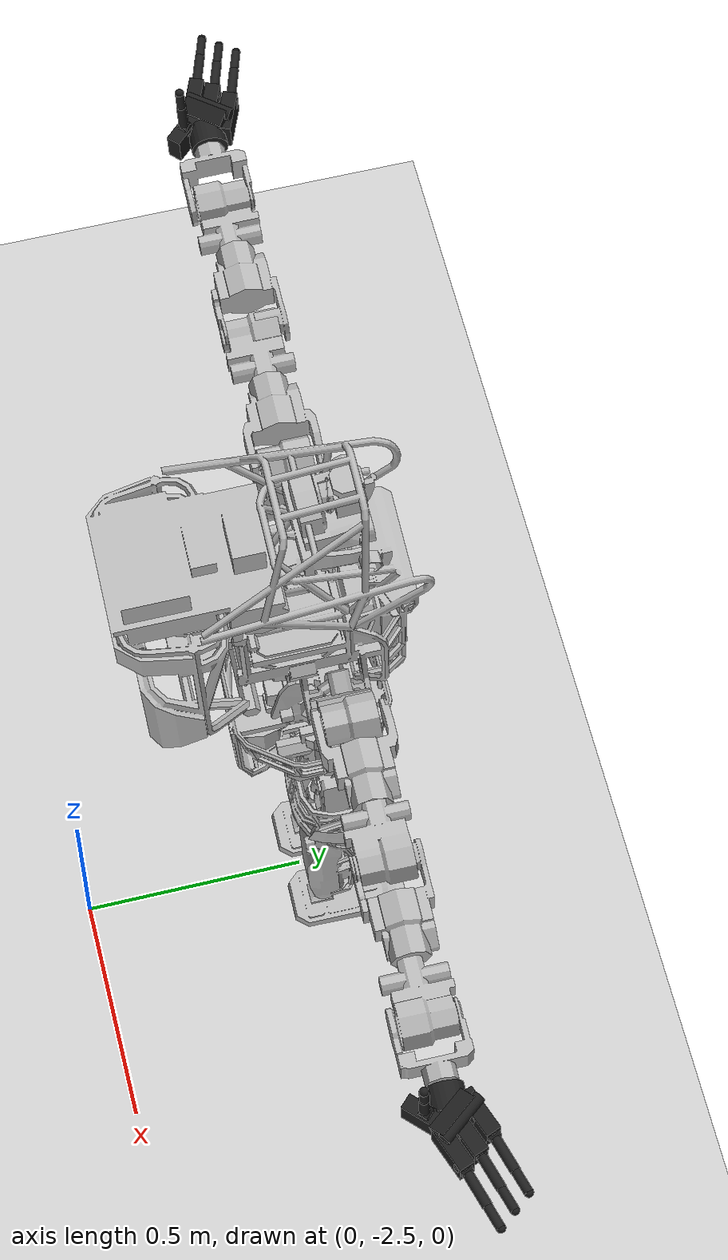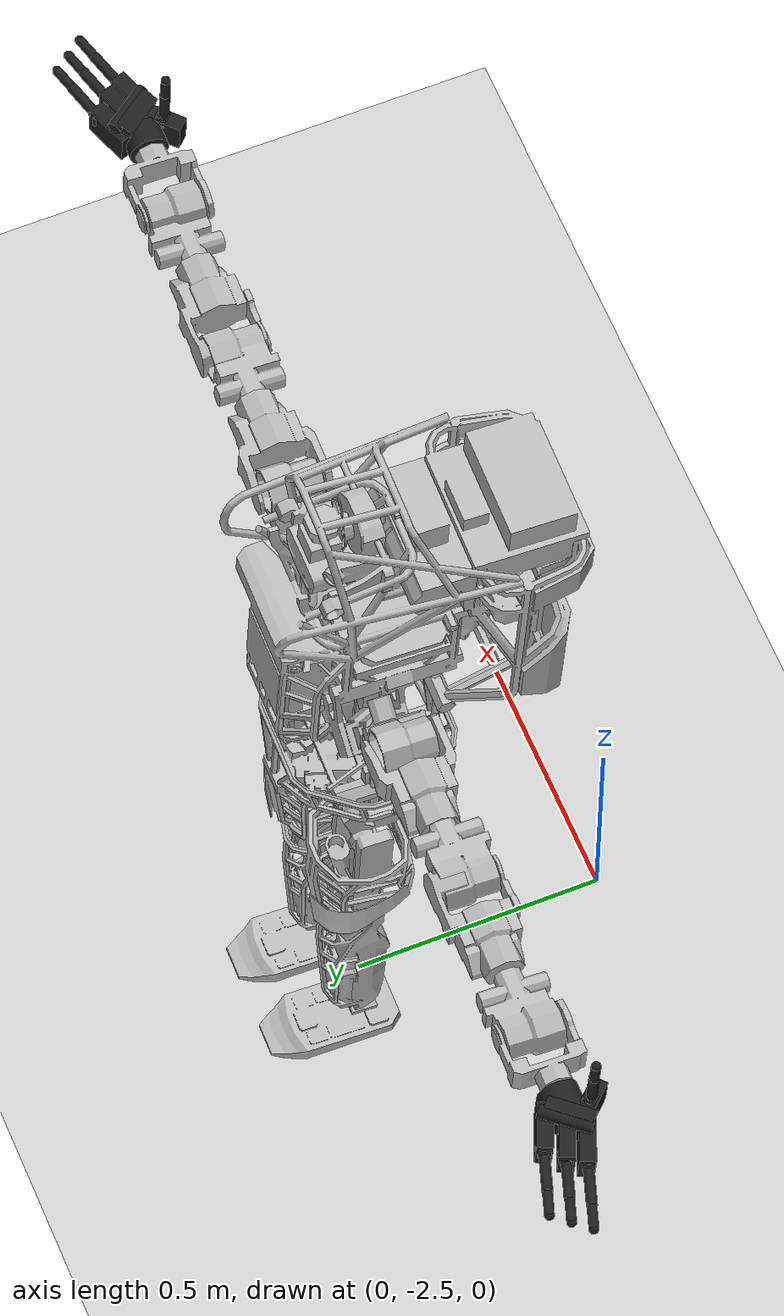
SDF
<sdf version="1.5">
 <world name="trials_task_7">
  <physics type="ode">
   <gravity>0 0 -9.81</gravity>
   <ode>
    <solver>
     <use_dynamic_moi_rescaling>1</use_dynamic_moi_rescaling>
     <type>quick</type>
     <iters>50</iters>
     <sor>1.4</sor>
    </solver>
    <constraints>
     <cfm>0</cfm>
     <erp>0.2</erp>
     <contact_max_correcting_vel>100</contact_max_correcting_vel>
     <contact_surface_layer>0</contact_surface_layer>
    </constraints>
   </ode>
   <real_time_update_rate>1000</real_time_update_rate>
   <max_step_size>0.001</max_step_size>
   <real_time_factor>1</real_time_factor>
   <magnetic_field>5.5645e-06 2.28758e-05 -4.23884e-05</magnetic_field>
  </physics>
  <light name="sun" type="directional">
   <pose>0 0 10 0 -0 0</pose>
   <diffuse>0.8 0.8 0.8 1</diffuse>
   <specular>0.1 0.1 0.1 1</specular>
   <attenuation>
    <range>1000</range>
    <constant>0.9</constant>
    <linear>0.01</linear>
    <quadratic>0.001</quadratic>
   </attenuation>
   <direction>-0.5 0.5 -1</direction>
  </light>
  <model name="ground_plane">
   <static>1</static>
   <link name="link">
    <collision name="collision">
     <geometry><plane><normal>0 0 1</normal><size>100 100</size></plane></geometry>
     <surface><friction><ode><mu>100</mu><mu2>50</mu2></ode></friction></surface>
    </collision>
    <visual name="visual">
     <cast_shadows>0</cast_shadows>
     <geometry><plane><normal>0 0 1</normal><size>100 100</size></plane></geometry>
     <material>
      <script><uri>file://media/materials/scripts/gazebo.material</uri><name>Gazebo/Grey</name></script>
     </material>
    </visual>
    <velocity_decay><linear>0</linear><angular>0</angular></velocity_decay>
   </link>
  </model>
  <plugin name="vrc_plugin" filename="libVRCPlugin.so">
   <atlas><model_name>atlas</model_name><pin_link>utorso</pin_link></atlas>
   <drc_vehicle>
    <model_name>drc_vehicle_xp900</model_name>
    <seat_link>polaris_ranger_xp900::chassis</seat_link>
   </drc_vehicle>
   <drc_fire_hose>
    <fire_hose_model>fire_hose</fire_hose_model>
    <coupling_link>coupling</coupling_link>
    <standpipe_model>standpipe</standpipe_model>
    <spout_link>standpipe</spout_link>
    <thread_pitch>-1000</thread_pitch>
    <coupling_relative_pose>1.17038e-05 -0.125623 0.35 -0.0412152 -1.57078 1.61199</coupling_relative_pose>
   </drc_fire_hose>
  </plugin>
  <scene><ambient>0.4 0.4 0.4 1</ambient><background>0.7 0.7 0.7 1</background><shadows>1</shadows></scene>
  <spherical_coordinates>
   <surface_model>EARTH_WGS84</surface_model>
   <latitude_deg>0</latitude_deg>
   <longitude_deg>0</longitude_deg>
   <elevation>0</elevation>
   <heading_deg>0</heading_deg>
  </spherical_coordinates>
  <model name="atlas">
   <link name="pelvis">
    <inertial>
     <pose>0.0113715 0 0.0268706 0 -0 0</pose>
     <mass>17.982</mass>
     <inertia>
      <ixx>0.125569</ixx>
      <ixy>0.0008</ixy>
      <ixz>-0.000499757</ixz>
      <iyy>0.0972062</iyy>
      <iyz>-0.0005</iyz>
      <izz>0.117937</izz>
     </inertia>
    </inertial>
    <collision name="pelvis_collision">
     <geometry>
      <mesh><scale>1 1 1</scale><uri>model://atlas_description/meshes_v3/pelvis.stl</uri></mesh>
     </geometry>
     <surface><friction><ode><mu>0.9</mu><mu2>0.9</mu2></ode></friction></surface>
    </collision>
    <visual name="pelvis_visual">
     <geometry>
      <mesh><scale>1 1 1</scale><uri>model://atlas_description/meshes_v3/pelvis.dae</uri></mesh>
     </geometry>
    </visual>
    <visual name="pelvis_visual_imu_link">
     <pose>0.0599153 0 -0.01415 0 -0 0</pose>
     <geometry><box><size>0.01 0.01 0.01</size></box></geometry>
    </visual>
    <velocity_decay><linear>0</linear><angular>0</angular></velocity_decay>
    <velocity_decay><linear>0</linear><angular>0</angular></velocity_decay>
    <sensor name="imu_sensor" type="imu">
     <always_on>1</always_on>
     <update_rate>1000</update_rate>
     <imu>
      <noise>
       <type>gaussian</type>
       <rate>
        <mean>0</mean>
        <stddev>0.0002</stddev>
        <bias_mean>7.5e-06</bias_mean>
        <bias_stddev>8e-07</bias_stddev>
       </rate>
       <accel><mean>0</mean><stddev>0.017</stddev><bias_mean>0.1</bias_mean><bias_stddev>0.001</bias_stddev></accel>
      </noise>
     </imu>
     <pose>0.0599153 0 -0.01415 0 -0 0</pose>
    </sensor>
   </link>
   <link name="ltorso">
    <pose>-0.0125 0 0 0 -0 0</pose>
    <inertial>
     <pose>-0.0112984 -3.15366e-06 0.0746835 0 -0 0</pose>
     <mass>2.409</mass>
     <inertia>
      <ixx>0.0039092</ixx>
      <ixy>-5.04491e-08</ixy>
      <ixz>-0.000342157</ixz>
      <iyy>0.00341694</iyy>
      <iyz>4.87119e-07</iyz>
      <izz>0.00174492</izz>
     </inertia>
    </inertial>
    <collision name="ltorso_collision">
     <geometry>
      <mesh><scale>1 1 1</scale><uri>model://atlas_description/meshes_v3/ltorso.stl</uri></mesh>
     </geometry>
     <surface><friction><ode><mu>0.9</mu><mu2>0.9</mu2></ode></friction></surface>
    </collision>
    <visual name="ltorso_visual">
     <geometry>
      <mesh><scale>1 1 1</scale><uri>model://atlas_description/meshes_v3/ltorso.dae</uri></mesh>
     </geometry>
    </visual>
    <velocity_decay><linear>0</linear><angular>0</angular></velocity_decay>
   </link>
   <joint name="back_bkz" type="revolute">
    <child>ltorso</child>
    <parent>pelvis</parent>
    <axis>
     <xyz>0 0 1</xyz>
     <limit><lower>-0.65</lower><upper>0.658</upper><effort>124.016</effort><velocity>12</velocity></limit>
     <dynamics>
      <damping>0.1</damping>
      <friction>0</friction>
      <spring_reference>0</spring_reference>
      <spring_stiffness>0</spring_stiffness>
     </dynamics>
     <use_parent_model_frame>1</use_parent_model_frame>
    </axis>
   </joint>
   <link name="mtorso">
    <pose>-0.0125 0 0.16197 0 -0 0</pose>
    <inertial>
     <pose>-0.00816266 -0.0131245 0.0305974 0 -0 0</pose>
     <mass>0.69</mass>
     <inertia>
      <ixx>0.000454181</ixx>
      <ixy>-6.10764e-05</ixy>
      <ixz>3.94009e-05</ixz>
      <iyy>0.000483282</iyy>
      <iyz>5.27463e-05</iyz>
      <izz>0.000444215</izz>
     </inertia>
    </inertial>
    <collision name="mtorso_collision">
     <geometry>
      <mesh><scale>1 1 1</scale><uri>model://atlas_description/meshes_v3/mtorso.stl</uri></mesh>
     </geometry>
     <surface><friction><ode><mu>0.9</mu><mu2>0.9</mu2></ode></friction></surface>
    </collision>
    <visual name="mtorso_visual">
     <geometry>
      <mesh><scale>1 1 1</scale><uri>model://atlas_description/meshes_v3/mtorso.dae</uri></mesh>
     </geometry>
    </visual>
    <velocity_decay><linear>0</linear><angular>0</angular></velocity_decay>
   </link>
   <joint name="back_bky" type="revolute">
    <child>mtorso</child>
    <parent>ltorso</parent>
    <axis>
     <xyz>0 1 0</xyz>
     <limit><lower>-0.611</lower><upper>0.437</upper><effort>206.843</effort><velocity>12</velocity></limit>
     <dynamics>
      <damping>0.1</damping>
      <friction>0</friction>
      <spring_reference>0</spring_reference>
      <spring_stiffness>0</spring_stiffness>
     </dynamics>
     <use_parent_model_frame>1</use_parent_model_frame>
    </axis>
   </joint>
   <link name="utorso">
    <pose>-0.0125 0 0.21197 0 -0 0</pose>
    <inertial>
     <pose>-0.0909481 5.04713e-05 0.301106 0 -0 0</pose>
     <mass>52.307</mass>
     <inertia>
      <ixx>1.4846</ixx>
      <ixy>0.00338676</ixy>
      <ixz>0.326214</ixz>
      <iyy>1.54533</iyy>
      <iyz>3.95833e-05</iyz>
      <izz>1.32284</izz>
     </inertia>
    </inertial>
    <collision name="utorso_collision">
     <geometry>
      <mesh><scale>1 1 1</scale><uri>model://atlas_description/meshes_v3/utorso.stl</uri></mesh>
     </geometry>
     <surface><friction><ode><mu>0.9</mu><mu2>0.9</mu2></ode></friction></surface>
    </collision>
    <collision name="utorso_collision_utorso_1">
     <geometry>
      <mesh><scale>1 1 1</scale><uri>model://atlas_description/meshes_v3/utorso_pack.stl</uri></mesh>
     </geometry>
     <surface><friction><ode><mu>0.9</mu><mu2>0.9</mu2></ode></friction></surface>
    </collision>
    <visual name="utorso_visual">
     <geometry>
      <mesh><scale>1 1 1</scale><uri>model://atlas_description/meshes_v3/utorso.dae</uri></mesh>
     </geometry>
    </visual>
    <visual name="utorso_visual_utorso_1">
     <geometry>
      <mesh><scale>1 1 1</scale><uri>model://atlas_description/meshes_v3/utorso_pack.dae</uri></mesh>
     </geometry>
    </visual>
    <visual name="utorso_visual_l_situational_awareness_camera_link">
     <pose>0.216409 0.121799 0.406759 -1.5708 5.55112e-17 1.309</pose>
     <geometry><box><size>0.01 0.01 0.01</size></box></geometry>
    </visual>
    <visual name="utorso_visual_r_situational_awareness_camera_link">
     <pose>0.216409 -0.121799 0.406759 1.5708 5.55112e-17 -1.309</pose>
     <geometry><box><size>0.01 0.01 0.01</size></box></geometry>
    </visual>
    <visual name="utorso_visual_rear_situational_awareness_camera_link">
     <pose>-0.0026 0.0264 0.6649 0 -0 3.14159</pose>
     <geometry><box><size>0.01 0.01 0.01</size></box></geometry>
    </visual>
    <velocity_decay><linear>0</linear><angular>0</angular></velocity_decay>
   </link>
   <joint name="back_bkx" type="revolute">
    <child>utorso</child>
    <parent>mtorso</parent>
    <axis>
     <xyz>1 0 0</xyz>
     <limit><lower>-0.697</lower><upper>0.572</upper><effort>200</effort><velocity>12</velocity></limit>
     <dynamics>
      <damping>0.1</damping>
      <friction>0</friction>
      <spring_reference>0</spring_reference>
      <spring_stiffness>0</spring_stiffness>
     </dynamics>
     <use_parent_model_frame>1</use_parent_model_frame>
    </axis>
   </joint>
   <link name="l_clav">
    <pose>0.05191 0.13866 0.31915 0 -0 0</pose>
    <inertial>
     <pose>0 0.048 0.084 0 -0 0</pose>
     <mass>3.45</mass>
     <inertia><ixx>0.011</ixx><ixy>0</ixy><ixz>0</ixz><iyy>0.009</iyy><iyz>-0.004</iyz><izz>0.004</izz></inertia>
    </inertial>
    <collision name="l_clav_collision">
     <geometry>
      <mesh><scale>1 1 1</scale><uri>model://atlas_description/meshes_v3/l_clav.stl</uri></mesh>
     </geometry>
     <surface><friction><ode><mu>0.9</mu><mu2>0.9</mu2></ode></friction></surface>
    </collision>
    <visual name="l_clav_visual">
     <geometry>
      <mesh><scale>1 1 1</scale><uri>model://atlas_description/meshes_v3/l_clav.dae</uri></mesh>
     </geometry>
    </visual>
    <velocity_decay><linear>0</linear><angular>0</angular></velocity_decay>
   </link>
   <joint name="l_arm_shy" type="revolute">
    <child>l_clav</child>
    <parent>utorso</parent>
    <axis>
     <xyz>0 0.5 0.866025</xyz>
     <limit><lower>-1.474</lower><upper>0.769</upper><effort>212</effort><velocity>12</velocity></limit>
     <dynamics>
      <damping>0.1</damping>
      <friction>0</friction>
      <spring_reference>0</spring_reference>
      <spring_stiffness>0</spring_stiffness>
     </dynamics>
     <use_parent_model_frame>1</use_parent_model_frame>
    </axis>
   </joint>
   <link name="l_scap">
    <pose>0.05191 0.27901 0.51524 0 -0 0</pose>
    <inertial>
     <mass>3.012</mass>
     <inertia><ixx>0.00319</ixx><ixy>0</ixy><ixz>0</ixz><iyy>0.00583</iyy><iyz>0</iyz><izz>0.00583</izz></inertia>
    </inertial>
    <collision name="l_scap_collision">
     <geometry>
      <mesh><scale>1 1 1</scale><uri>model://atlas_description/meshes_v3/l_scap.stl</uri></mesh>
     </geometry>
     <surface><friction><ode><mu>0.9</mu><mu2>0.9</mu2></ode></friction></surface>
    </collision>
    <visual name="l_scap_visual">
     <geometry>
      <mesh><scale>1 1 1</scale><uri>model://atlas_description/meshes_v3/l_scap.dae</uri></mesh>
     </geometry>
    </visual>
    <velocity_decay><linear>0</linear><angular>0</angular></velocity_decay>
   </link>
   <joint name="l_arm_shx" type="revolute">
    <child>l_scap</child>
    <parent>l_clav</parent>
    <axis>
     <xyz>1 0 0</xyz>
     <limit><lower>-1.473</lower><upper>1.524</upper><effort>170</effort><velocity>12</velocity></limit>
     <dynamics>
      <damping>0.1</damping>
      <friction>0</friction>
      <spring_reference>0</spring_reference>
      <spring_stiffness>0</spring_stiffness>
     </dynamics>
     <use_parent_model_frame>1</use_parent_model_frame>
    </axis>
    <physics>
     <ode>
      <implicit_spring_damper>1</implicit_spring_damper>
      <cfm_damping>1</cfm_damping>
      <limit><cfm>0</cfm><erp>0.2</erp></limit>
     </ode>
    </physics>
   </joint>
   <link name="l_uarm">
    <pose>0.05191 0.46601 0.53124 0 -0 0</pose>
    <inertial>
     <pose>0 -0.065 0 0 -0 0</pose>
     <mass>3.388</mass>
     <inertia><ixx>0.00656</ixx><ixy>0</ixy><ixz>0</ixz><iyy>0.00358</iyy><iyz>0</iyz><izz>0.00656</izz></inertia>
    </inertial>
    <collision name="l_uarm_collision">
     <geometry>
      <mesh><scale>1 1 1</scale><uri>model://atlas_description/meshes_v3/l_uarm.stl</uri></mesh>
     </geometry>
     <surface><friction><ode><mu>0.9</mu><mu2>0.9</mu2></ode></friction></surface>
    </collision>
    <visual name="l_uarm_visual">
     <geometry>
      <mesh><scale>1 1 1</scale><uri>model://atlas_description/meshes_v3/l_uarm.dae</uri></mesh>
     </geometry>
    </visual>
    <velocity_decay><linear>0</linear><angular>0</angular></velocity_decay>
   </link>
   <joint name="l_arm_ely" type="revolute">
    <child>l_uarm</child>
    <parent>l_scap</parent>
    <axis>
     <xyz>0 1 0</xyz>
     <limit><lower>0.044</lower><upper>3.117</upper><effort>114</effort><velocity>12</velocity></limit>
     <dynamics>
      <damping>0.1</damping>
      <friction>0</friction>
      <spring_reference>0</spring_reference>
      <spring_stiffness>0</spring_stiffness>
     </dynamics>
     <use_parent_model_frame>1</use_parent_model_frame>
    </axis>
    <physics>
     <ode>
      <implicit_spring_damper>1</implicit_spring_damper>
      <cfm_damping>1</cfm_damping>
      <limit><cfm>0</cfm><erp>0.2</erp></limit>
     </ode>
    </physics>
   </joint>
   <link name="l_larm">
    <pose>0.05191 0.58501 0.54045 0 -0 0</pose>
    <inertial>
     <mass>2.509</mass>
     <inertia><ixx>0.00265</ixx><ixy>0</ixy><ixz>0</ixz><iyy>0.00446</iyy><iyz>0</iyz><izz>0.00446</izz></inertia>
    </inertial>
    <collision name="l_larm_collision">
     <geometry>
      <mesh><scale>1 1 1</scale><uri>model://atlas_description/meshes_v3/l_larm.stl</uri></mesh>
     </geometry>
     <surface><friction><ode><mu>0.9</mu><mu2>0.9</mu2></ode></friction></surface>
    </collision>
    <visual name="l_larm_visual">
     <geometry>
      <mesh><scale>1 1 1</scale><uri>model://atlas_description/meshes_v3/l_larm.dae</uri></mesh>
     </geometry>
    </visual>
    <velocity_decay><linear>0</linear><angular>0</angular></velocity_decay>
   </link>
   <joint name="l_arm_elx" type="revolute">
    <child>l_larm</child>
    <parent>l_uarm</parent>
    <axis>
     <xyz>1 0 0</xyz>
     <limit><lower>0.023</lower><upper>2.35</upper><effort>114</effort><velocity>12</velocity></limit>
     <dynamics>
      <damping>0.1</damping>
      <friction>0</friction>
      <spring_reference>0</spring_reference>
      <spring_stiffness>0</spring_stiffness>
     </dynamics>
     <use_parent_model_frame>1</use_parent_model_frame>
    </axis>
    <physics>
     <ode>
      <implicit_spring_damper>1</implicit_spring_damper>
      <cfm_damping>1</cfm_damping>
      <limit><cfm>0</cfm><erp>0.2</erp></limit>
     </ode>
    </physics>
   </joint>
   <link name="l_farm">
    <pose>0.05191 0.77201 0.53124 0 -0 0</pose>
    <inertial>
     <pose>0 -0.065 0 0 -0 0</pose>
     <mass>3.388</mass>
     <inertia><ixx>0.00656</ixx><ixy>0</ixy><ixz>0</ixz><iyy>0.00358</iyy><iyz>0</iyz><izz>0.00656</izz></inertia>
    </inertial>
    <collision name="l_farm_collision">
     <geometry>
      <mesh><scale>1 1 1</scale><uri>model://atlas_description/meshes_v3/l_farm.stl</uri></mesh>
     </geometry>
     <surface><friction><ode><mu>0.9</mu><mu2>0.9</mu2></ode></friction></surface>
    </collision>
    <visual name="l_farm_visual">
     <geometry>
      <mesh><scale>1 1 1</scale><uri>model://atlas_description/meshes_v3/l_farm.dae</uri></mesh>
     </geometry>
    </visual>
    <velocity_decay><linear>0</linear><angular>0</angular></velocity_decay>
   </link>
   <joint name="l_arm_wry" type="revolute">
    <child>l_farm</child>
    <parent>l_larm</parent>
    <axis>
     <xyz>0 1 0</xyz>
     <limit><lower>0.028</lower><upper>3.035</upper><effort>114</effort><velocity>12</velocity></limit>
     <dynamics>
      <damping>0.1</damping>
      <friction>0</friction>
      <spring_reference>0</spring_reference>
      <spring_stiffness>0</spring_stiffness>
     </dynamics>
     <use_parent_model_frame>1</use_parent_model_frame>
    </axis>
   </joint>
   <link name="l_hand">
    <pose>0.05191 0.89101 0.54045 0 -0 0</pose>
    <inertial>
     <pose>0.00355825 0.086034 0.006451 0 -0 0</pose>
     <mass>4.87201</mass>
     <inertia>
      <ixx>0.0494183</ixx>
      <ixy>-0.00292444</ixy>
      <ixz>2.43133e-05</ixz>
      <iyy>0.00805207</iyy>
      <iyz>-0.00287079</iyz>
      <izz>0.0527051</izz>
     </inertia>
    </inertial>
    <collision name="l_hand_collision">
     <geometry>
      <mesh><scale>1 1 1</scale><uri>model://atlas_description/meshes_v3/l_hand.stl</uri></mesh>
     </geometry>
     <surface><friction><ode><mu>0.9</mu><mu2>0.9</mu2></ode></friction></surface>
    </collision>
    <collision name="l_hand_collision_left_palm">
     <pose>0.0177904 0.20416 0.04976 -3.14157 1.57079 -0.670783</pose>
     <geometry><cylinder><length>0.1</length><radius>0.013</radius></cylinder></geometry>
     <surface><friction><ode><mu>0.9</mu><mu2>0.9</mu2></ode></friction></surface>
     <max_contacts>6</max_contacts>
     <surface>
      <contact><ode><kp>1e+06</kp><kd>1</kd><max_vel>0.1</max_vel><min_depth>0</min_depth></ode></contact>
      <friction><ode><mu>1.1</mu><mu2>1.1</mu2></ode></friction>
     </surface>
    </collision>
    <collision name="l_hand_collision_left_palm_1">
     <pose>0.0097904 0.19916 0.03276 -0.41 8.32667e-17 2.47079</pose>
     <geometry><box><size>0.09 0.035 0.05</size></box></geometry>
     <surface><friction><ode><mu>0.9</mu><mu2>0.9</mu2></ode></friction></surface>
    </collision>
    <collision name="l_hand_collision_left_palm_2">
     <pose>0.00179013 0.15516 0.00676 3.14158 1.57079 -1.57082</pose>
     <geometry><cylinder><length>0.05</length><radius>0.038</radius></cylinder></geometry>
     <surface><friction><ode><mu>0.9</mu><mu2>0.9</mu2></ode></friction></surface>
    </collision>
    <collision name="l_hand_collision_left_palm_3">
     <pose>-0.0082093 0.24516 0.00676 0 -0 1.20079</pose>
     <geometry><box><size>0.09 0.03 0.06</size></box></geometry>
     <surface><friction><ode><mu>0.9</mu><mu2>0.9</mu2></ode></friction></surface>
    </collision>
    <collision name="l_hand_collision_left_palm_4">
     <pose>0.0217906 0.22516 0.00676 0 -0 1.20079</pose>
     <geometry><box><size>0.09 0.03 0.06</size></box></geometry>
     <surface><friction><ode><mu>0.9</mu><mu2>0.9</mu2></ode></friction></surface>
    </collision>
    <collision name="l_hand_collision_left_palm_5">
     <pose>0.0517904 0.19516 0.00676 0 -0 1.20079</pose>
     <geometry><box><size>0.09 0.03 0.06</size></box></geometry>
     <surface><friction><ode><mu>0.9</mu><mu2>0.9</mu2></ode></friction></surface>
    </collision>
    <collision name="l_hand_collision_left_palm_6">
     <pose>-0.0382097 0.17916 0.00676 0 -0 0.78079</pose>
     <geometry><box><size>0.09 0.03 0.06</size></box></geometry>
     <surface><friction><ode><mu>0.9</mu><mu2>0.9</mu2></ode></friction></surface>
    </collision>
    <visual name="l_hand_visual">
     <geometry>
      <mesh><scale>1 1 1</scale><uri>model://atlas_description/meshes_v3/l_hand.dae</uri></mesh>
     </geometry>
    </visual>
    <visual name="l_hand_visual_left_palm">
     <pose>0.0177904 0.20416 0.04976 -3.14157 1.57079 -0.670783</pose>
     <geometry><cylinder><length>0.1</length><radius>0.013</radius></cylinder></geometry>
     <material><script><name>Gazebo/FlatBlack</name><uri>__default__</uri></script></material>
    </visual>
    <visual name="l_hand_visual_left_palm_1">
     <pose>0.0097904 0.19916 0.03276 -0.41 8.32667e-17 2.47079</pose>
     <geometry><box><size>0.09 0.035 0.05</size></box></geometry>
     <material><script><name>Gazebo/FlatBlack</name><uri>__default__</uri></script></material>
    </visual>
    <visual name="l_hand_visual_left_palm_2">
     <pose>0.00179013 0.15516 0.00676 3.14158 1.57079 -1.57082</pose>
     <geometry><cylinder><length>0.05</length><radius>0.038</radius></cylinder></geometry>
     <material><script><name>Gazebo/FlatBlack</name><uri>__default__</uri></script></material>
    </visual>
    <visual name="l_hand_visual_left_palm_3">
     <pose>-0.0082093 0.24516 0.00676 0 -0 1.20079</pose>
     <geometry><box><size>0.09 0.03 0.06</size></box></geometry>
     <material><script><name>Gazebo/FlatBlack</name><uri>__default__</uri></script></material>
    </visual>
    <visual name="l_hand_visual_left_palm_4">
     <pose>0.0217906 0.22516 0.00676 0 -0 1.20079</pose>
     <geometry><box><size>0.09 0.03 0.06</size></box></geometry>
     <material><script><name>Gazebo/FlatBlack</name><uri>__default__</uri></script></material>
    </visual>
    <visual name="l_hand_visual_left_palm_5">
     <pose>0.0517904 0.19516 0.00676 0 -0 1.20079</pose>
     <geometry><box><size>0.09 0.03 0.06</size></box></geometry>
     <material><script><name>Gazebo/FlatBlack</name><uri>__default__</uri></script></material>
    </visual>
    <visual name="l_hand_visual_left_palm_6">
     <pose>-0.0382097 0.17916 0.00676 0 -0 0.78079</pose>
     <geometry><box><size>0.09 0.03 0.06</size></box></geometry>
     <material><script><name>Gazebo/FlatBlack</name><uri>__default__</uri></script></material>
    </visual>
    <visual name="l_hand_visual_left_palm_left_camera_frame">
     <pose>0.0469576 0.178673 0.03676 2.47075 -1.57079 1.57083</pose>
     <geometry><box><size>0.003 0.01 0.007</size></box></geometry>
     <material><script><name>Gazebo/FlatBlack</name><uri>__default__</uri></script></material>
    </visual>
    <visual name="l_hand_visual_left_palm_right_camera_frame">
     <pose>0.0156247 0.203537 0.03676 2.47075 -1.57079 1.57083</pose>
     <geometry><box><size>0.003 0.01 0.007</size></box></geometry>
     <material><script><name>Gazebo/FlatBlack</name><uri>__default__</uri></script></material>
    </visual>
    <velocity_decay><linear>0</linear><angular>0</angular></velocity_decay>
    <sensor name="imu_sensor" type="imu">
     <always_on>1</always_on>
     <update_rate>1000</update_rate>
     <imu>
      <noise>
       <type>gaussian</type>
       <rate>
        <mean>0</mean>
        <stddev>0.0002</stddev>
        <bias_mean>7.5e-06</bias_mean>
        <bias_stddev>8e-07</bias_stddev>
       </rate>
       <accel><mean>0</mean><stddev>0.017</stddev><bias_mean>0.1</bias_mean><bias_stddev>0.001</bias_stddev></accel>
      </noise>
     </imu>
    </sensor>
    <velocity_decay><linear>0</linear><angular>0</angular></velocity_decay>
    <velocity_decay><linear>0</linear><angular>0</angular></velocity_decay>
    <velocity_decay><linear>0</linear><angular>0</angular></velocity_decay>
    <velocity_decay><linear>0</linear><angular>0</angular></velocity_decay>
    <velocity_decay><linear>0</linear><angular>0</angular></velocity_decay>
    <velocity_decay><linear>0</linear><angular>0</angular></velocity_decay>
    <velocity_decay><linear>0</linear><angular>0</angular></velocity_decay>
    <sensor name="left_palm_stereo_camera" type="multicamera">
     <update_rate>30</update_rate>
     <camera name="left">
      <horizontal_fov>1.25664</horizontal_fov>
      <image><width>752</width><height>480</height><format>L8</format></image>
      <clip><near>0.02</near><far>100</far></clip>
      <noise><type>gaussian</type><mean>0</mean><stddev>0.007</stddev></noise>
     </camera>
     <camera name="right">
      <pose>0 -0.04 0 0 -0 0</pose>
      <horizontal_fov>1.25664</horizontal_fov>
      <image><width>752</width><height>480</height><format>L8</format></image>
      <clip><near>0.02</near><far>100</far></clip>
      <noise><type>gaussian</type><mean>0</mean><stddev>0.007</stddev></noise>
     </camera>
     <plugin name="stereo_camera_controller" filename="libgazebo_ros_multicamera.so">
      <alwaysOn>true</alwaysOn>
      <updateRate>0.0</updateRate>
      <cameraName>sandia_hands/l_hand</cameraName>
      <imageTopicName>image_raw</imageTopicName>
      <cameraInfoTopicName>camera_info</cameraInfoTopicName>
      <frameName>left_palm_left_camera_optical_frame</frameName>
      <hackBaseline>0.04</hackBaseline>
      <distortionK1>0.0</distortionK1>
      <distortionK2>0.0</distortionK2>
      <distortionK3>0.0</distortionK3>
      <distortionT1>0.0</distortionT1>
      <distortionT2>0.0</distortionT2>
     </plugin>
     <pose>0.0469576 0.178673 0.03676 2.47075 -1.57079 1.57083</pose>
    </sensor>
   </link>
   <joint name="l_arm_wrx" type="revolute">
    <child>l_hand</child>
    <parent>l_farm</parent>
    <axis>
     <xyz>1 0 0</xyz>
     <limit><lower>-1.163</lower><upper>0.977</upper><effort>60</effort><velocity>12</velocity></limit>
     <dynamics>
      <damping>0.1</damping>
      <friction>0</friction>
      <spring_reference>0</spring_reference>
      <spring_stiffness>0</spring_stiffness>
     </dynamics>
     <use_parent_model_frame>1</use_parent_model_frame>
    </axis>
   </joint>
   <link name="left_f0_0">
    <pose>0.0537009 1.16617 0.55221 0 -0 1.27079</pose>
    <inertial>
     <mass>0.106</mass>
     <inertia>
      <ixx>1.1925e-05</ixx>
      <ixy>0</ixy>
      <ixz>0</ixz>
      <iyy>0.00011505</iyy>
      <iyz>0</iyz>
      <izz>0.00011505</izz>
     </inertia>
    </inertial>
    <collision name="left_f0_0_collision">
     <pose>0 0 0.003 0 -0 0</pose>
     <geometry><cylinder><length>0.023</length><radius>0.015</radius></cylinder></geometry>
     <max_contacts>1</max_contacts>
     <surface>
      <contact><ode><kp>1e+06</kp><kd>10</kd><max_vel>0.1</max_vel><min_depth>0</min_depth></ode></contact>
      <friction><ode><mu>1.1</mu><mu2>1.1</mu2></ode></friction>
     </surface>
    </collision>
    <collision name="left_f0_0_collision_left_f0_0_other">
     <pose>0.011 0 0.003 1.5708 -0 0</pose>
     <geometry><cylinder><length>0.023</length><radius>0.01</radius></cylinder></geometry>
     <max_contacts>1</max_contacts>
     <surface>
      <contact><ode><kp>1e+06</kp><kd>10</kd><max_vel>0.1</max_vel><min_depth>0</min_depth></ode></contact>
      <friction><ode><mu>1.1</mu><mu2>1.1</mu2></ode></friction>
     </surface>
    </collision>
    <visual name="left_f0_0_visual">
     <pose>0 0 0.003 0 -0 0</pose>
     <geometry><cylinder><length>0.023</length><radius>0.015</radius></cylinder></geometry>
     <material><script><name>Gazebo/FlatBlack</name><uri>__default__</uri></script></material>
    </visual>
    <visual name="left_f0_0_visual_left_f0_0_1">
     <pose>0.011 0 0.003 1.5708 -0 0</pose>
     <geometry><cylinder><length>0.023</length><radius>0.01</radius></cylinder></geometry>
     <material><script><name>Gazebo/FlatBlack</name><uri>__default__</uri></script></material>
    </visual>
    <velocity_decay><linear>0</linear><angular>0</angular></velocity_decay>
   </link>
   <joint name="left_f0_j0" type="revolute">
    <child>left_f0_0</child>
    <parent>l_hand</parent>
    <axis>
     <xyz>0 0 -1</xyz>
     <limit><lower>-1.5708</lower><upper>1.5708</upper><effort>11</effort><velocity>-1</velocity></limit>
     <dynamics>
      <damping>1</damping>
      <friction>0</friction>
      <spring_reference>0</spring_reference>
      <spring_stiffness>0</spring_stiffness>
     </dynamics>
     <use_parent_model_frame>1</use_parent_model_frame>
    </axis>
    <physics>
     <ode>
      <implicit_spring_damper>1</implicit_spring_damper>
      <cfm_damping>1</cfm_damping>
      <limit><cfm>0</cfm><erp>0.2</erp></limit>
     </ode>
    </physics>
   </joint>
   <link name="left_f0_1">
    <pose>0.0619756 1.19292 0.55221 1.5708 2.22045e-16 1.27079</pose>
    <inertial>
     <pose>0.00697674 0 0 0 -0 0</pose>
     <mass>0.043</mass>
     <inertia>
      <ixx>2.65e-06</ixx>
      <ixy>0</ixy>
      <ixz>0</ixz>
      <iyy>2.10767e-05</iyy>
      <iyz>0</iyz>
      <izz>2.10767e-05</izz>
     </inertia>
    </inertial>
    <collision name="left_f0_1_collision">
     <pose>0.024 0 0 3.14159 1.57079 3.14159</pose>
     <geometry><cylinder><length>0.067</length><radius>0.01</radius></cylinder></geometry>
     <max_contacts>1</max_contacts>
     <surface>
      <contact><ode><kp>1e+06</kp><kd>10</kd><max_vel>0.1</max_vel><min_depth>0</min_depth></ode></contact>
      <friction><ode><mu>1.1</mu><mu2>1.1</mu2></ode></friction>
     </surface>
    </collision>
    <visual name="left_f0_1_visual">
     <pose>0.024 0 0 3.14159 1.57079 3.14159</pose>
     <geometry><cylinder><length>0.067</length><radius>0.01</radius></cylinder></geometry>
     <material><script><name>Gazebo/FlatBlack</name><uri>__default__</uri></script></material>
    </visual>
    <velocity_decay><linear>0</linear><angular>0</angular></velocity_decay>
   </link>
   <joint name="left_f0_j1" type="revolute">
    <child>left_f0_1</child>
    <parent>left_f0_0</parent>
    <axis>
     <xyz>0.955335 -0.295526 0</xyz>
     <limit><lower>-1.5708</lower><upper>1.5708</upper><effort>28</effort><velocity>-1</velocity></limit>
     <dynamics>
      <damping>1</damping>
      <friction>0</friction>
      <spring_reference>0</spring_reference>
      <spring_stiffness>0</spring_stiffness>
     </dynamics>
     <use_parent_model_frame>1</use_parent_model_frame>
    </axis>
    <physics>
     <ode>
      <implicit_spring_damper>1</implicit_spring_damper>
      <cfm_damping>1</cfm_damping>
      <limit><cfm>0</cfm><erp>0.2</erp></limit>
     </ode>
    </physics>
   </joint>
   <link name="left_f0_2">
    <pose>0.0767519 1.24069 0.55221 1.5708 2.22045e-16 1.27079</pose>
    <inertial>
     <pose>0.00930233 0 0 0 -0 0</pose>
     <mass>0.043</mass>
     <inertia>
      <ixx>2.3365e-06</ixx>
      <ixy>0</ixy>
      <ixz>0</ixz>
      <iyy>2.28821e-05</iyy>
      <iyz>0</iyz>
      <izz>2.28821e-05</izz>
     </inertia>
    </inertial>
    <collision name="left_f0_2_collision">
     <pose>0.024 0 0 3.14159 1.57079 3.14159</pose>
     <geometry><cylinder><length>0.057</length><radius>0.009</radius></cylinder></geometry>
     <max_contacts>1</max_contacts>
     <surface>
      <contact><ode><kp>1e+06</kp><kd>10</kd><max_vel>0.1</max_vel><min_depth>0</min_depth></ode></contact>
      <friction><ode><mu>1.1</mu><mu2>1.1</mu2></ode></friction>
     </surface>
    </collision>
    <collision name="left_f0_2_collision_left_f0_2_other">
     <pose>0.052 0 0 0 -0 0</pose>
     <geometry><sphere><radius>0.009</radius></sphere></geometry>
     <max_contacts>1</max_contacts>
     <surface>
      <contact><ode><kp>1e+06</kp><kd>10</kd><max_vel>0.1</max_vel><min_depth>0</min_depth></ode></contact>
      <friction><ode><mu>1.1</mu><mu2>1.1</mu2></ode></friction>
     </surface>
    </collision>
    <visual name="left_f0_2_visual">
     <pose>0.024 0 0 3.14159 1.57079 3.14159</pose>
     <geometry><cylinder><length>0.057</length><radius>0.009</radius></cylinder></geometry>
     <material><script><name>Gazebo/FlatBlack</name><uri>__default__</uri></script></material>
    </visual>
    <visual name="left_f0_2_visual_left_f0_2_1">
     <pose>0.052 0 0 0 -0 0</pose>
     <geometry><sphere><radius>0.009</radius></sphere></geometry>
     <material><script><name>Gazebo/FlatBlack</name><uri>__default__</uri></script></material>
    </visual>
    <velocity_decay><linear>0</linear><angular>0</angular></velocity_decay>
   </link>
   <joint name="left_f0_j2" type="revolute">
    <child>left_f0_2</child>
    <parent>left_f0_1</parent>
    <axis>
     <xyz>0.955335 -0.295526 0</xyz>
     <limit><lower>-1.5708</lower><upper>1.5708</upper><effort>28</effort><velocity>-1</velocity></limit>
     <dynamics>
      <damping>1</damping>
      <friction>0</friction>
      <spring_reference>0</spring_reference>
      <spring_stiffness>0</spring_stiffness>
     </dynamics>
     <use_parent_model_frame>1</use_parent_model_frame>
    </axis>
    <physics>
     <ode>
      <implicit_spring_damper>1</implicit_spring_damper>
      <cfm_damping>1</cfm_damping>
      <limit><cfm>0</cfm><erp>0.2</erp></limit>
     </ode>
    </physics>
   </joint>
   <link name="left_f1_0">
    <pose>0.0849207 1.14117 0.55221 0 -0 1.27079</pose>
    <inertial>
     <mass>0.106</mass>
     <inertia>
      <ixx>1.1925e-05</ixx>
      <ixy>0</ixy>
      <ixz>0</ixz>
      <iyy>0.00011505</iyy>
      <iyz>0</iyz>
      <izz>0.00011505</izz>
     </inertia>
    </inertial>
    <collision name="left_f1_0_collision">
     <pose>0 0 0.003 0 -0 0</pose>
     <geometry><cylinder><length>0.023</length><radius>0.015</radius></cylinder></geometry>
     <max_contacts>1</max_contacts>
     <surface>
      <contact><ode><kp>1e+06</kp><kd>10</kd><max_vel>0.1</max_vel><min_depth>0</min_depth></ode></contact>
      <friction><ode><mu>1.1</mu><mu2>1.1</mu2></ode></friction>
     </surface>
    </collision>
    <collision name="left_f1_0_collision_left_f1_0_other">
     <pose>0.011 0 0.003 1.5708 -0 0</pose>
     <geometry><cylinder><length>0.023</length><radius>0.01</radius></cylinder></geometry>
     <max_contacts>1</max_contacts>
     <surface>
      <contact><ode><kp>1e+06</kp><kd>10</kd><max_vel>0.1</max_vel><min_depth>0</min_depth></ode></contact>
      <friction><ode><mu>1.1</mu><mu2>1.1</mu2></ode></friction>
     </surface>
    </collision>
    <visual name="left_f1_0_visual">
     <pose>0 0 0.003 0 -0 0</pose>
     <geometry><cylinder><length>0.023</length><radius>0.015</radius></cylinder></geometry>
     <material><script><name>Gazebo/FlatBlack</name><uri>__default__</uri></script></material>
    </visual>
    <visual name="left_f1_0_visual_left_f1_0_1">
     <pose>0.011 0 0.003 1.5708 -0 0</pose>
     <geometry><cylinder><length>0.023</length><radius>0.01</radius></cylinder></geometry>
     <material><script><name>Gazebo/FlatBlack</name><uri>__default__</uri></script></material>
    </visual>
    <velocity_decay><linear>0</linear><angular>0</angular></velocity_decay>
   </link>
   <joint name="left_f1_j0" type="revolute">
    <child>left_f1_0</child>
    <parent>l_hand</parent>
    <axis>
     <xyz>0 0 -1</xyz>
     <limit><lower>-1.5708</lower><upper>1.5708</upper><effort>11</effort><velocity>-1</velocity></limit>
     <dynamics>
      <damping>1</damping>
      <friction>0</friction>
      <spring_reference>0</spring_reference>
      <spring_stiffness>0</spring_stiffness>
     </dynamics>
     <use_parent_model_frame>1</use_parent_model_frame>
    </axis>
    <physics>
     <ode>
      <implicit_spring_damper>1</implicit_spring_damper>
      <cfm_damping>1</cfm_damping>
      <limit><cfm>0</cfm><erp>0.2</erp></limit>
     </ode>
    </physics>
   </joint>
   <link name="left_f1_1">
    <pose>0.0931955 1.16792 0.55221 1.5708 2.22045e-16 1.27079</pose>
    <inertial>
     <pose>0.00697674 0 0 0 -0 0</pose>
     <mass>0.043</mass>
     <inertia>
      <ixx>2.65e-06</ixx>
      <ixy>0</ixy>
      <ixz>0</ixz>
      <iyy>2.10767e-05</iyy>
      <iyz>0</iyz>
      <izz>2.10767e-05</izz>
     </inertia>
    </inertial>
    <collision name="left_f1_1_collision">
     <pose>0.024 0 0 3.14159 1.57079 3.14159</pose>
     <geometry><cylinder><length>0.067</length><radius>0.01</radius></cylinder></geometry>
     <max_contacts>1</max_contacts>
     <surface>
      <contact><ode><kp>1e+06</kp><kd>10</kd><max_vel>0.1</max_vel><min_depth>0</min_depth></ode></contact>
      <friction><ode><mu>1.1</mu><mu2>1.1</mu2></ode></friction>
     </surface>
    </collision>
    <visual name="left_f1_1_visual">
     <pose>0.024 0 0 3.14159 1.57079 3.14159</pose>
     <geometry><cylinder><length>0.067</length><radius>0.01</radius></cylinder></geometry>
     <material><script><name>Gazebo/FlatBlack</name><uri>__default__</uri></script></material>
    </visual>
    <velocity_decay><linear>0</linear><angular>0</angular></velocity_decay>
   </link>
   <joint name="left_f1_j1" type="revolute">
    <child>left_f1_1</child>
    <parent>left_f1_0</parent>
    <axis>
     <xyz>0.955335 -0.295526 0</xyz>
     <limit><lower>-1.5708</lower><upper>1.5708</upper><effort>28</effort><velocity>-1</velocity></limit>
     <dynamics>
      <damping>1</damping>
      <friction>0</friction>
      <spring_reference>0</spring_reference>
      <spring_stiffness>0</spring_stiffness>
     </dynamics>
     <use_parent_model_frame>1</use_parent_model_frame>
    </axis>
    <physics>
     <ode>
      <implicit_spring_damper>1</implicit_spring_damper>
      <cfm_damping>1</cfm_damping>
      <limit><cfm>0</cfm><erp>0.2</erp></limit>
     </ode>
    </physics>
   </joint>
   <link name="left_f1_2">
    <pose>0.107972 1.21569 0.55221 1.5708 2.22045e-16 1.27079</pose>
    <inertial>
     <pose>0.00930233 0 0 0 -0 0</pose>
     <mass>0.043</mass>
     <inertia>
      <ixx>2.3365e-06</ixx>
      <ixy>0</ixy>
      <ixz>0</ixz>
      <iyy>2.28821e-05</iyy>
      <iyz>0</iyz>
      <izz>2.28821e-05</izz>
     </inertia>
    </inertial>
    <collision name="left_f1_2_collision">
     <pose>0.024 0 0 3.14159 1.57079 3.14159</pose>
     <geometry><cylinder><length>0.057</length><radius>0.009</radius></cylinder></geometry>
     <max_contacts>1</max_contacts>
     <surface>
      <contact><ode><kp>1e+06</kp><kd>10</kd><max_vel>0.1</max_vel><min_depth>0</min_depth></ode></contact>
      <friction><ode><mu>1.1</mu><mu2>1.1</mu2></ode></friction>
     </surface>
    </collision>
    <collision name="left_f1_2_collision_left_f1_2_other">
     <pose>0.052 0 0 0 -0 0</pose>
     <geometry><sphere><radius>0.009</radius></sphere></geometry>
     <max_contacts>1</max_contacts>
     <surface>
      <contact><ode><kp>1e+06</kp><kd>10</kd><max_vel>0.1</max_vel><min_depth>0</min_depth></ode></contact>
      <friction><ode><mu>1.1</mu><mu2>1.1</mu2></ode></friction>
     </surface>
    </collision>
    <visual name="left_f1_2_visual">
     <pose>0.024 0 0 3.14159 1.57079 3.14159</pose>
     <geometry><cylinder><length>0.057</length><radius>0.009</radius></cylinder></geometry>
     <material><script><name>Gazebo/FlatBlack</name><uri>__default__</uri></script></material>
    </visual>
    <visual name="left_f1_2_visual_left_f1_2_1">
     <pose>0.052 0 0 0 -0 0</pose>
     <geometry><sphere><radius>0.009</radius></sphere></geometry>
     <material><script><name>Gazebo/FlatBlack</name><uri>__default__</uri></script></material>
    </visual>
    <velocity_decay><linear>0</linear><angular>0</angular></velocity_decay>
   </link>
   <joint name="left_f1_j2" type="revolute">
    <child>left_f1_2</child>
    <parent>left_f1_1</parent>
    <axis>
     <xyz>0.955335 -0.295526 0</xyz>
     <limit><lower>-1.5708</lower><upper>1.5708</upper><effort>28</effort><velocity>-1</velocity></limit>
     <dynamics>
      <damping>1</damping>
      <friction>0</friction>
      <spring_reference>0</spring_reference>
      <spring_stiffness>0</spring_stiffness>
     </dynamics>
     <use_parent_model_frame>1</use_parent_model_frame>
    </axis>
    <physics>
     <ode>
      <implicit_spring_damper>1</implicit_spring_damper>
      <cfm_damping>1</cfm_damping>
      <limit><cfm>0</cfm><erp>0.2</erp></limit>
     </ode>
    </physics>
   </joint>
   <link name="left_f2_0">
    <pose>0.116151 1.11617 0.55221 0 -0 1.27079</pose>
    <inertial>
     <mass>0.106</mass>
     <inertia>
      <ixx>1.1925e-05</ixx>
      <ixy>0</ixy>
      <ixz>0</ixz>
      <iyy>0.00011505</iyy>
      <iyz>0</iyz>
      <izz>0.00011505</izz>
     </inertia>
    </inertial>
    <collision name="left_f2_0_collision">
     <pose>0 0 0.003 0 -0 0</pose>
     <geometry><cylinder><length>0.023</length><radius>0.015</radius></cylinder></geometry>
     <max_contacts>1</max_contacts>
     <surface>
      <contact><ode><kp>1e+06</kp><kd>10</kd><max_vel>0.1</max_vel><min_depth>0</min_depth></ode></contact>
      <friction><ode><mu>1.1</mu><mu2>1.1</mu2></ode></friction>
     </surface>
    </collision>
    <collision name="left_f2_0_collision_left_f2_0_other">
     <pose>0.011 0 0.003 1.5708 -0 0</pose>
     <geometry><cylinder><length>0.023</length><radius>0.01</radius></cylinder></geometry>
     <max_contacts>1</max_contacts>
     <surface>
      <contact><ode><kp>1e+06</kp><kd>10</kd><max_vel>0.1</max_vel><min_depth>0</min_depth></ode></contact>
      <friction><ode><mu>1.1</mu><mu2>1.1</mu2></ode></friction>
     </surface>
    </collision>
    <visual name="left_f2_0_visual">
     <pose>0 0 0.003 0 -0 0</pose>
     <geometry><cylinder><length>0.023</length><radius>0.015</radius></cylinder></geometry>
     <material><script><name>Gazebo/FlatBlack</name><uri>__default__</uri></script></material>
    </visual>
    <visual name="left_f2_0_visual_left_f2_0_1">
     <pose>0.011 0 0.003 1.5708 -0 0</pose>
     <geometry><cylinder><length>0.023</length><radius>0.01</radius></cylinder></geometry>
     <material><script><name>Gazebo/FlatBlack</name><uri>__default__</uri></script></material>
    </visual>
    <velocity_decay><linear>0</linear><angular>0</angular></velocity_decay>
   </link>
   <joint name="left_f2_j0" type="revolute">
    <child>left_f2_0</child>
    <parent>l_hand</parent>
    <axis>
     <xyz>0 0 -1</xyz>
     <limit><lower>-1.5708</lower><upper>1.5708</upper><effort>11</effort><velocity>-1</velocity></limit>
     <dynamics>
      <damping>1</damping>
      <friction>0</friction>
      <spring_reference>0</spring_reference>
      <spring_stiffness>0</spring_stiffness>
     </dynamics>
     <use_parent_model_frame>1</use_parent_model_frame>
    </axis>
    <physics>
     <ode>
      <implicit_spring_damper>1</implicit_spring_damper>
      <cfm_damping>1</cfm_damping>
      <limit><cfm>0</cfm><erp>0.2</erp></limit>
     </ode>
    </physics>
   </joint>
   <link name="left_f2_1">
    <pose>0.124425 1.14292 0.55221 1.5708 2.22045e-16 1.27079</pose>
    <inertial>
     <pose>0.00697674 0 0 0 -0 0</pose>
     <mass>0.043</mass>
     <inertia>
      <ixx>2.65e-06</ixx>
      <ixy>0</ixy>
      <ixz>0</ixz>
      <iyy>2.10767e-05</iyy>
      <iyz>0</iyz>
      <izz>2.10767e-05</izz>
     </inertia>
    </inertial>
    <collision name="left_f2_1_collision">
     <pose>0.024 0 0 3.14159 1.57079 3.14159</pose>
     <geometry><cylinder><length>0.067</length><radius>0.01</radius></cylinder></geometry>
     <max_contacts>1</max_contacts>
     <surface>
      <contact><ode><kp>1e+06</kp><kd>10</kd><max_vel>0.1</max_vel><min_depth>0</min_depth></ode></contact>
      <friction><ode><mu>1.1</mu><mu2>1.1</mu2></ode></friction>
     </surface>
    </collision>
    <visual name="left_f2_1_visual">
     <pose>0.024 0 0 3.14159 1.57079 3.14159</pose>
     <geometry><cylinder><length>0.067</length><radius>0.01</radius></cylinder></geometry>
     <material><script><name>Gazebo/FlatBlack</name><uri>__default__</uri></script></material>
    </visual>
    <velocity_decay><linear>0</linear><angular>0</angular></velocity_decay>
   </link>
   <joint name="left_f2_j1" type="revolute">
    <child>left_f2_1</child>
    <parent>left_f2_0</parent>
    <axis>
     <xyz>0.955335 -0.295526 0</xyz>
     <limit><lower>-1.5708</lower><upper>1.5708</upper><effort>28</effort><velocity>-1</velocity></limit>
     <dynamics>
      <damping>1</damping>
      <friction>0</friction>
      <spring_reference>0</spring_reference>
      <spring_stiffness>0</spring_stiffness>
     </dynamics>
     <use_parent_model_frame>1</use_parent_model_frame>
    </axis>
    <physics>
     <ode>
      <implicit_spring_damper>1</implicit_spring_damper>
      <cfm_damping>1</cfm_damping>
      <limit><cfm>0</cfm><erp>0.2</erp></limit>
     </ode>
    </physics>
   </joint>
   <link name="left_f2_2">
    <pose>0.139202 1.19069 0.55221 1.5708 2.22045e-16 1.27079</pose>
    <inertial>
     <pose>0.00930233 0 0 0 -0 0</pose>
     <mass>0.043</mass>
     <inertia>
      <ixx>2.3365e-06</ixx>
      <ixy>0</ixy>
      <ixz>0</ixz>
      <iyy>2.28821e-05</iyy>
      <iyz>0</iyz>
      <izz>2.28821e-05</izz>
     </inertia>
    </inertial>
    <collision name="left_f2_2_collision">
     <pose>0.024 0 0 3.14159 1.57079 3.14159</pose>
     <geometry><cylinder><length>0.057</length><radius>0.009</radius></cylinder></geometry>
     <max_contacts>1</max_contacts>
     <surface>
      <contact><ode><kp>1e+06</kp><kd>10</kd><max_vel>0.1</max_vel><min_depth>0</min_depth></ode></contact>
      <friction><ode><mu>1.1</mu><mu2>1.1</mu2></ode></friction>
     </surface>
    </collision>
    <collision name="left_f2_2_collision_left_f2_2_other">
     <pose>0.052 0 0 0 -0 0</pose>
     <geometry><sphere><radius>0.009</radius></sphere></geometry>
     <max_contacts>1</max_contacts>
     <surface>
      <contact><ode><kp>1e+06</kp><kd>10</kd><max_vel>0.1</max_vel><min_depth>0</min_depth></ode></contact>
      <friction><ode><mu>1.1</mu><mu2>1.1</mu2></ode></friction>
     </surface>
    </collision>
    <visual name="left_f2_2_visual">
     <pose>0.024 0 0 3.14159 1.57079 3.14159</pose>
     <geometry><cylinder><length>0.057</length><radius>0.009</radius></cylinder></geometry>
     <material><script><name>Gazebo/FlatBlack</name><uri>__default__</uri></script></material>
    </visual>
    <visual name="left_f2_2_visual_left_f2_2_1">
     <pose>0.052 0 0 0 -0 0</pose>
     <geometry><sphere><radius>0.009</radius></sphere></geometry>
     <material><script><name>Gazebo/FlatBlack</name><uri>__default__</uri></script></material>
    </visual>
    <velocity_decay><linear>0</linear><angular>0</angular></velocity_decay>
   </link>
   <joint name="left_f2_j2" type="revolute">
    <child>left_f2_2</child>
    <parent>left_f2_1</parent>
    <axis>
     <xyz>0.955335 -0.295526 0</xyz>
     <limit><lower>-1.5708</lower><upper>1.5708</upper><effort>28</effort><velocity>-1</velocity></limit>
     <dynamics>
      <damping>1</damping>
      <friction>0</friction>
      <spring_reference>0</spring_reference>
      <spring_stiffness>0</spring_stiffness>
     </dynamics>
     <use_parent_model_frame>1</use_parent_model_frame>
    </axis>
    <physics>
     <ode>
      <implicit_spring_damper>1</implicit_spring_damper>
      <cfm_damping>1</cfm_damping>
      <limit><cfm>0</cfm><erp>0.2</erp></limit>
     </ode>
    </physics>
   </joint>
   <link name="left_f3_0">
    <pose>0.00987025 1.06612 0.56621 3.14158 -1.57079 0.785413</pose>
    <inertial>
     <mass>0.106</mass>
     <inertia>
      <ixx>1.1925e-05</ixx>
      <ixy>0</ixy>
      <ixz>0</ixz>
      <iyy>0.00011505</iyy>
      <iyz>0</iyz>
      <izz>0.00011505</izz>
     </inertia>
    </inertial>
    <collision name="left_f3_0_collision">
     <pose>0 0 0.003 0 -0 0</pose>
     <geometry><cylinder><length>0.023</length><radius>0.015</radius></cylinder></geometry>
     <max_contacts>1</max_contacts>
     <surface>
      <contact><ode><kp>1e+06</kp><kd>10</kd><max_vel>0.1</max_vel><min_depth>0</min_depth></ode></contact>
      <friction><ode><mu>1.1</mu><mu2>1.1</mu2></ode></friction>
     </surface>
    </collision>
    <collision name="left_f3_0_collision_left_f3_0_other">
     <pose>0.011 0 0.003 1.5708 -0 0</pose>
     <geometry><cylinder><length>0.023</length><radius>0.01</radius></cylinder></geometry>
     <max_contacts>1</max_contacts>
     <surface>
      <contact><ode><kp>1e+06</kp><kd>10</kd><max_vel>0.1</max_vel><min_depth>0</min_depth></ode></contact>
      <friction><ode><mu>1.1</mu><mu2>1.1</mu2></ode></friction>
     </surface>
    </collision>
    <visual name="left_f3_0_visual">
     <pose>0 0 0.003 0 -0 0</pose>
     <geometry><cylinder><length>0.023</length><radius>0.015</radius></cylinder></geometry>
     <material><script><name>Gazebo/FlatBlack</name><uri>__default__</uri></script></material>
    </visual>
    <visual name="left_f3_0_visual_left_f3_0_1">
     <pose>0.011 0 0.003 1.5708 -0 0</pose>
     <geometry><cylinder><length>0.023</length><radius>0.01</radius></cylinder></geometry>
     <material><script><name>Gazebo/FlatBlack</name><uri>__default__</uri></script></material>
    </visual>
    <velocity_decay><linear>0</linear><angular>0</angular></velocity_decay>
   </link>
   <joint name="left_f3_j0" type="revolute">
    <child>left_f3_0</child>
    <parent>l_hand</parent>
    <axis>
     <xyz>-0.707107 -0.707106 -0</xyz>
     <limit><lower>-1.5708</lower><upper>1.5708</upper><effort>11</effort><velocity>-1</velocity></limit>
     <dynamics>
      <damping>1</damping>
      <friction>0</friction>
      <spring_reference>0</spring_reference>
      <spring_stiffness>0</spring_stiffness>
     </dynamics>
     <use_parent_model_frame>1</use_parent_model_frame>
    </axis>
    <physics>
     <ode>
      <implicit_spring_damper>1</implicit_spring_damper>
      <cfm_damping>1</cfm_damping>
      <limit><cfm>0</cfm><erp>0.2</erp></limit>
     </ode>
    </physics>
   </joint>
   <link name="left_f3_1">
    <pose>0.00987025 1.06612 0.59421 -1.5708 -1.57079 0.785403</pose>
    <inertial>
     <pose>0.00697674 0 0 0 -0 0</pose>
     <mass>0.043</mass>
     <inertia>
      <ixx>2.65e-06</ixx>
      <ixy>0</ixy>
      <ixz>0</ixz>
      <iyy>2.10767e-05</iyy>
      <iyz>0</iyz>
      <izz>2.10767e-05</izz>
     </inertia>
    </inertial>
    <collision name="left_f3_1_collision">
     <pose>0.024 0 0 3.14159 1.57079 3.14159</pose>
     <geometry><cylinder><length>0.067</length><radius>0.01</radius></cylinder></geometry>
     <max_contacts>1</max_contacts>
     <surface>
      <contact><ode><kp>1e+06</kp><kd>10</kd><max_vel>0.1</max_vel><min_depth>0</min_depth></ode></contact>
      <friction><ode><mu>1.1</mu><mu2>1.1</mu2></ode></friction>
     </surface>
    </collision>
    <visual name="left_f3_1_visual">
     <pose>0.024 0 0 3.14159 1.57079 3.14159</pose>
     <geometry><cylinder><length>0.067</length><radius>0.01</radius></cylinder></geometry>
     <material><script><name>Gazebo/FlatBlack</name><uri>__default__</uri></script></material>
    </visual>
    <velocity_decay><linear>0</linear><angular>0</angular></velocity_decay>
   </link>
   <joint name="left_f3_j1" type="revolute">
    <child>left_f3_1</child>
    <parent>left_f3_0</parent>
    <axis>
     <xyz>-0.707106 0.707107 -0</xyz>
     <limit><lower>-1.5708</lower><upper>1.5708</upper><effort>28</effort><velocity>-1</velocity></limit>
     <dynamics>
      <damping>1</damping>
      <friction>0</friction>
      <spring_reference>0</spring_reference>
      <spring_stiffness>0</spring_stiffness>
     </dynamics>
     <use_parent_model_frame>1</use_parent_model_frame>
    </axis>
    <physics>
     <ode>
      <implicit_spring_damper>1</implicit_spring_damper>
      <cfm_damping>1</cfm_damping>
      <limit><cfm>0</cfm><erp>0.2</erp></limit>
     </ode>
    </physics>
   </joint>
   <link name="left_f3_2">
    <pose>0.00987025 1.06612 0.64421 -1.5708 -1.57079 0.785403</pose>
    <inertial>
     <pose>0.00930233 0 0 0 -0 0</pose>
     <mass>0.043</mass>
     <inertia>
      <ixx>2.3365e-06</ixx>
      <ixy>0</ixy>
      <ixz>0</ixz>
      <iyy>2.28821e-05</iyy>
      <iyz>0</iyz>
      <izz>2.28821e-05</izz>
     </inertia>
    </inertial>
    <collision name="left_f3_2_collision">
     <pose>0.024 0 0 3.14159 1.57079 3.14159</pose>
     <geometry><cylinder><length>0.057</length><radius>0.009</radius></cylinder></geometry>
     <max_contacts>1</max_contacts>
     <surface>
      <contact><ode><kp>1e+06</kp><kd>10</kd><max_vel>0.1</max_vel><min_depth>0</min_depth></ode></contact>
      <friction><ode><mu>1.1</mu><mu2>1.1</mu2></ode></friction>
     </surface>
    </collision>
    <collision name="left_f3_2_collision_left_f3_2_other">
     <pose>0.052 0 0 0 -0 0</pose>
     <geometry><sphere><radius>0.009</radius></sphere></geometry>
     <max_contacts>1</max_contacts>
     <surface>
      <contact><ode><kp>1e+06</kp><kd>10</kd><max_vel>0.1</max_vel><min_depth>0</min_depth></ode></contact>
      <friction><ode><mu>1.1</mu><mu2>1.1</mu2></ode></friction>
     </surface>
    </collision>
    <visual name="left_f3_2_visual">
     <pose>0.024 0 0 3.14159 1.57079 3.14159</pose>
     <geometry><cylinder><length>0.057</length><radius>0.009</radius></cylinder></geometry>
     <material><script><name>Gazebo/FlatBlack</name><uri>__default__</uri></script></material>
    </visual>
    <visual name="left_f3_2_visual_left_f3_2_1">
     <pose>0.052 0 0 0 -0 0</pose>
     <geometry><sphere><radius>0.009</radius></sphere></geometry>
     <material><script><name>Gazebo/FlatBlack</name><uri>__default__</uri></script></material>
    </visual>
    <velocity_decay><linear>0</linear><angular>0</angular></velocity_decay>
   </link>
   <joint name="left_f3_j2" type="revolute">
    <child>left_f3_2</child>
    <parent>left_f3_1</parent>
    <axis>
     <xyz>-0.707106 0.707107 -0</xyz>
     <limit><lower>-1.5708</lower><upper>1.5708</upper><effort>28</effort><velocity>-1</velocity></limit>
     <dynamics>
      <damping>1</damping>
      <friction>0</friction>
      <spring_reference>0</spring_reference>
      <spring_stiffness>0</spring_stiffness>
     </dynamics>
     <use_parent_model_frame>1</use_parent_model_frame>
    </axis>
    <physics>
     <ode>
      <implicit_spring_damper>1</implicit_spring_damper>
      <cfm_damping>1</cfm_damping>
      <limit><cfm>0</cfm><erp>0.2</erp></limit>
     </ode>
    </physics>
   </joint>
   <link name="head">
    <pose>0.1375 0.01 0.78197 -0.03 -0.025659 0.02</pose>
    <inertial>
     <pose>-0.0754942 3.38765e-05 0.0277411 0 -0 0</pose>
     <mass>1.41991</mass>
     <inertia>
      <ixx>0.00361284</ixx>
      <ixy>-1.51324e-06</ixy>
      <ixz>-0.000892818</ixz>
      <iyy>0.00208745</iyy>
      <iyz>-6.83342e-07</iyz>
      <izz>0.00179047</izz>
     </inertia>
    </inertial>
    <collision name="head_collision">
     <pose>-0.0503 0 -0.00195 0 -0 0</pose>
     <geometry><box><size>0.1311 0.12 0.0591</size></box></geometry>
     <surface><friction><ode><mu>0.9</mu><mu2>0.9</mu2></ode></friction></surface>
    </collision>
    <collision name="head_collision_head_other">
     <pose>-0.093 0 0.0868 0 -0 0</pose>
     <geometry><box><size>0.0468 0.12 0.1184</size></box></geometry>
     <surface><friction><ode><mu>0.9</mu><mu2>0.9</mu2></ode></friction></surface>
    </collision>
    <visual name="head_visual">
     <geometry>
      <mesh><scale>1 1 1</scale><uri>model://multisense_sl_description/meshes/head.dae</uri></mesh>
     </geometry>
    </visual>
    <visual name="head_visual_head_imu_link">
     <pose>-0.0475 0.035 0 0 -0 0</pose>
     <geometry><box><size>0.01 0.01 0.01</size></box></geometry>
    </visual>
    <velocity_decay><linear>0</linear><angular>0</angular></velocity_decay>
    <velocity_decay><linear>0</linear><angular>0</angular></velocity_decay>
    <sensor name="head_imu_sensor" type="imu">
     <always_on>1</always_on>
     <update_rate>1000</update_rate>
     <imu>
      <noise>
       <type>gaussian</type>
       <rate>
        <mean>0</mean>
        <stddev>0.0002</stddev>
        <bias_mean>7.5e-06</bias_mean>
        <bias_stddev>8e-07</bias_stddev>
       </rate>
       <accel><mean>0</mean><stddev>0.017</stddev><bias_mean>0.1</bias_mean><bias_stddev>0.001</bias_stddev></accel>
      </noise>
     </imu>
     <pose>-0.0475 0.035 0 0 -0 0</pose>
    </sensor>
    <velocity_decay><linear>0</linear><angular>0</angular></velocity_decay>
    <sensor name="stereo_camera" type="multicamera">
     <update_rate>30</update_rate>
     <camera name="left">
      <horizontal_fov>1.39626</horizontal_fov>
      <image><width>800</width><height>800</height><format>R8G8B8</format></image>
      <clip><near>0.02</near><far>300</far></clip>
      <noise><type>gaussian</type><mean>0</mean><stddev>0.007</stddev></noise>
     </camera>
     <camera name="right">
      <pose>0 -0.07 0 0 -0 0</pose>
      <horizontal_fov>1.39626</horizontal_fov>
      <image><width>800</width><height>800</height><format>R8G8B8</format></image>
      <clip><near>0.02</near><far>300</far></clip>
      <noise><type>gaussian</type><mean>0</mean><stddev>0.007</stddev></noise>
     </camera>
     <plugin name="stereo_camera_controller" filename="libgazebo_ros_multicamera.so">
      <alwaysOn>true</alwaysOn>
      <updateRate>0.0</updateRate>
      <cameraName>multisense_sl</cameraName>
      <imageTopicName>image_raw</imageTopicName>
      <cameraInfoTopicName>camera_info</cameraInfoTopicName>
      <frameName>left_camera_optical_frame</frameName>
      <hackBaseline>0.07</hackBaseline>
      <distortionK1>0.0</distortionK1>
      <distortionK2>0.0</distortionK2>
      <distortionK3>0.0</distortionK3>
      <distortionT1>0.0</distortionT1>
      <distortionT2>0.0</distortionT2>
     </plugin>
     <pose>0 0.035 -0.002 0 -0 0</pose>
    </sensor>
   </link>
   <joint name="neck_ry" type="revolute">
    <child>head</child>
    <parent>utorso</parent>
    <axis>
     <xyz>-0.01922 0.999366 -0.029986</xyz>
     <limit><lower>-0.547</lower><upper>1.157</upper><effort>5</effort><velocity>12</velocity></limit>
     <dynamics>
      <damping>0.1</damping>
      <friction>0</friction>
      <spring_reference>0</spring_reference>
      <spring_stiffness>0</spring_stiffness>
     </dynamics>
     <use_parent_model_frame>1</use_parent_model_frame>
    </axis>
   </joint>
   <link name="hokuyo_link">
    <pose>0.0906145 0.0117023 0.868757 -0.03 -0.025659 0.02</pose>
    <inertial>
     <pose>0.0324349 0.0004084 -0.0041783 0 -0 0</pose>
     <mass>0.057664</mass>
     <inertia>
      <ixx>3.8183e-05</ixx>
      <ixy>4.9927e-08</ixy>
      <ixz>1.1003e-05</ixz>
      <iyy>4.3437e-05</iyy>
      <iyz>-9.8165e-09</iyz>
      <izz>4.2686e-05</izz>
     </inertia>
    </inertial>
    <collision name="hokuyo_link_collision">
     <pose>0.01885 0 -0.02119 0 -0 0</pose>
     <geometry><box><size>0.08 0.06 0.04238</size></box></geometry>
     <surface><friction><ode><mu>0.9</mu><mu2>0.9</mu2></ode></friction></surface>
    </collision>
    <collision name="hokuyo_link_collision_hokuyo_link_other">
     <pose>0.03 0 0.0235 0 -0 0</pose>
     <geometry><cylinder><length>0.047</length><radius>0.024425</radius></cylinder></geometry>
     <surface><friction><ode><mu>0.9</mu><mu2>0.9</mu2></ode></friction></surface>
    </collision>
    <visual name="hokuyo_link_visual">
     <pose>0.045 -0.0261018 -0.0834237 -0.314 0 0</pose>
     <geometry>
      <mesh><scale>1 1 1</scale><uri>model://multisense_sl_description/meshes/head_camera.dae</uri></mesh>
     </geometry>
    </visual>
    <velocity_decay><linear>0</linear><angular>0</angular></velocity_decay>
    <velocity_decay><linear>0</linear><angular>0</angular></velocity_decay>
    <sensor name="head_hokuyo_sensor" type="ray">
     <visualize>0</visualize>
     <update_rate>40</update_rate>
     <ray>
      <scan>
       <horizontal>
        <samples>720</samples>
        <resolution>1</resolution>
        <min_angle>-1.5708</min_angle>
        <max_angle>1.5708</max_angle>
       </horizontal>
      </scan>
      <range><min>0.1</min><max>30</max><resolution>0.01</resolution></range>
      <noise><type>gaussian</type><mean>0</mean><stddev>0.01</stddev></noise>
     </ray>
     <plugin name="gazebo_ros_head_hokuyo_controller" filename="libgazebo_ros_laser.so">
      <topicName>/laser/scan</topicName>
      <frameName>head_hokuyo_frame</frameName>
     </plugin>
     <pose>0.03 0 0.015 0 -0 0</pose>
    </sensor>
   </link>
   <joint name="hokuyo_joint" type="revolute">
    <child>hokuyo_link</child>
    <parent>head</parent>
    <axis>
     <xyz>0.999471 0.019992 0.025656</xyz>
     <limit><lower>-1e+16</lower><upper>1e+16</upper></limit>
     <dynamics>
      <damping>0.01</damping>
      <friction>0</friction>
      <spring_reference>0</spring_reference>
      <spring_stiffness>0</spring_stiffness>
     </dynamics>
     <use_parent_model_frame>1</use_parent_model_frame>
    </axis>
    <physics>
     <ode>
      <implicit_spring_damper>1</implicit_spring_damper>
      <cfm_damping>1</cfm_damping>
      <limit><cfm>0</cfm><erp>0.2</erp></limit>
     </ode>
    </physics>
   </joint>
   <link name="r_clav">
    <pose>0.05191 -0.13866 0.31915 0 -0 0</pose>
    <inertial>
     <pose>0 -0.048 0.084 0 -0 0</pose>
     <mass>3.45</mass>
     <inertia><ixx>0.011</ixx><ixy>0</ixy><ixz>0</ixz><iyy>0.009</iyy><iyz>0.004</iyz><izz>0.004</izz></inertia>
    </inertial>
    <collision name="r_clav_collision">
     <geometry>
      <mesh><scale>1 1 1</scale><uri>model://atlas_description/meshes_v3/r_clav.stl</uri></mesh>
     </geometry>
     <surface><friction><ode><mu>0.9</mu><mu2>0.9</mu2></ode></friction></surface>
    </collision>
    <visual name="r_clav_visual">
     <geometry>
      <mesh><scale>1 1 1</scale><uri>model://atlas_description/meshes_v3/r_clav.dae</uri></mesh>
     </geometry>
    </visual>
    <velocity_decay><linear>0</linear><angular>0</angular></velocity_decay>
   </link>
   <joint name="r_arm_shy" type="revolute">
    <child>r_clav</child>
    <parent>utorso</parent>
    <axis>
     <xyz>0 0.5 -0.866025</xyz>
     <limit><lower>-1.576</lower><upper>0.676</upper><effort>212</effort><velocity>12</velocity></limit>
     <dynamics>
      <damping>0.1</damping>
      <friction>0</friction>
      <spring_reference>0</spring_reference>
      <spring_stiffness>0</spring_stiffness>
     </dynamics>
     <use_parent_model_frame>1</use_parent_model_frame>
    </axis>
   </joint>
   <link name="r_scap">
    <pose>0.05191 -0.27901 0.51524 0 -0 0</pose>
    <inertial>
     <mass>3.012</mass>
     <inertia><ixx>0.00319</ixx><ixy>0</ixy><ixz>0</ixz><iyy>0.00583</iyy><iyz>0</iyz><izz>0.00583</izz></inertia>
    </inertial>
    <collision name="r_scap_collision">
     <geometry>
      <mesh><scale>1 1 1</scale><uri>model://atlas_description/meshes_v3/r_scap.stl</uri></mesh>
     </geometry>
     <surface><friction><ode><mu>0.9</mu><mu2>0.9</mu2></ode></friction></surface>
    </collision>
    <visual name="r_scap_visual">
     <geometry>
      <mesh><scale>1 1 1</scale><uri>model://atlas_description/meshes_v3/r_scap.dae</uri></mesh>
     </geometry>
    </visual>
    <velocity_decay><linear>0</linear><angular>0</angular></velocity_decay>
   </link>
   <joint name="r_arm_shx" type="revolute">
    <child>r_scap</child>
    <parent>r_clav</parent>
    <axis>
     <xyz>1 0 0</xyz>
     <limit><lower>-1.563</lower><upper>1.487</upper><effort>170</effort><velocity>12</velocity></limit>
     <dynamics>
      <damping>0.1</damping>
      <friction>0</friction>
      <spring_reference>0</spring_reference>
      <spring_stiffness>0</spring_stiffness>
     </dynamics>
     <use_parent_model_frame>1</use_parent_model_frame>
    </axis>
    <physics>
     <ode>
      <implicit_spring_damper>1</implicit_spring_damper>
      <cfm_damping>1</cfm_damping>
      <limit><cfm>0</cfm><erp>0.2</erp></limit>
     </ode>
    </physics>
   </joint>
   <link name="r_uarm">
    <pose>0.05191 -0.46601 0.53124 0 -0 0</pose>
    <inertial>
     <pose>0 0.065 0 0 -0 0</pose>
     <mass>3.388</mass>
     <inertia><ixx>0.00656</ixx><ixy>0</ixy><ixz>0</ixz><iyy>0.00358</iyy><iyz>0</iyz><izz>0.00656</izz></inertia>
    </inertial>
    <collision name="r_uarm_collision">
     <geometry>
      <mesh><scale>1 1 1</scale><uri>model://atlas_description/meshes_v3/r_uarm.stl</uri></mesh>
     </geometry>
     <surface><friction><ode><mu>0.9</mu><mu2>0.9</mu2></ode></friction></surface>
    </collision>
    <visual name="r_uarm_visual">
     <geometry>
      <mesh><scale>1 1 1</scale><uri>model://atlas_description/meshes_v3/r_uarm.dae</uri></mesh>
     </geometry>
    </visual>
    <velocity_decay><linear>0</linear><angular>0</angular></velocity_decay>
   </link>
   <joint name="r_arm_ely" type="revolute">
    <child>r_uarm</child>
    <parent>r_scap</parent>
    <axis>
     <xyz>0 1 0</xyz>
     <limit><lower>0.01</lower><upper>3.028</upper><effort>114</effort><velocity>12</velocity></limit>
     <dynamics>
      <damping>0.1</damping>
      <friction>0</friction>
      <spring_reference>0</spring_reference>
      <spring_stiffness>0</spring_stiffness>
     </dynamics>
     <use_parent_model_frame>1</use_parent_model_frame>
    </axis>
    <physics>
     <ode>
      <implicit_spring_damper>1</implicit_spring_damper>
      <cfm_damping>1</cfm_damping>
      <limit><cfm>0</cfm><erp>0.2</erp></limit>
     </ode>
    </physics>
   </joint>
   <link name="r_larm">
    <pose>0.05191 -0.58501 0.54045 0 -0 0</pose>
    <inertial>
     <mass>2.509</mass>
     <inertia><ixx>0.00265</ixx><ixy>0</ixy><ixz>0</ixz><iyy>0.00446</iyy><iyz>0</iyz><izz>0.00446</izz></inertia>
    </inertial>
    <collision name="r_larm_collision">
     <geometry>
      <mesh><scale>1 1 1</scale><uri>model://atlas_description/meshes_v3/r_larm.stl</uri></mesh>
     </geometry>
     <surface><friction><ode><mu>0.9</mu><mu2>0.9</mu2></ode></friction></surface>
    </collision>
    <visual name="r_larm_visual">
     <geometry>
      <mesh><scale>1 1 1</scale><uri>model://atlas_description/meshes_v3/r_larm.dae</uri></mesh>
     </geometry>
    </visual>
    <velocity_decay><linear>0</linear><angular>0</angular></velocity_decay>
   </link>
   <joint name="r_arm_elx" type="revolute">
    <child>r_larm</child>
    <parent>r_uarm</parent>
    <axis>
     <xyz>1 0 0</xyz>
     <limit><lower>-2.342</lower><upper>0.033</upper><effort>114</effort><velocity>12</velocity></limit>
     <dynamics>
      <damping>0.1</damping>
      <friction>0</friction>
      <spring_reference>0</spring_reference>
      <spring_stiffness>0</spring_stiffness>
     </dynamics>
     <use_parent_model_frame>1</use_parent_model_frame>
    </axis>
    <physics>
     <ode>
      <implicit_spring_damper>1</implicit_spring_damper>
      <cfm_damping>1</cfm_damping>
      <limit><cfm>0</cfm><erp>0.2</erp></limit>
     </ode>
    </physics>
   </joint>
   <link name="r_farm">
    <pose>0.05191 -0.77201 0.53124 0 -0 0</pose>
    <inertial>
     <pose>0 0.065 0 0 -0 0</pose>
     <mass>3.388</mass>
     <inertia><ixx>0.00656</ixx><ixy>0</ixy><ixz>0</ixz><iyy>0.00358</iyy><iyz>0</iyz><izz>0.00656</izz></inertia>
    </inertial>
    <collision name="r_farm_collision">
     <geometry>
      <mesh><scale>1 1 1</scale><uri>model://atlas_description/meshes_v3/r_farm.stl</uri></mesh>
     </geometry>
     <surface><friction><ode><mu>0.9</mu><mu2>0.9</mu2></ode></friction></surface>
    </collision>
    <visual name="r_farm_visual">
     <geometry>
      <mesh><scale>1 1 1</scale><uri>model://atlas_description/meshes_v3/r_farm.dae</uri></mesh>
     </geometry>
    </visual>
    <velocity_decay><linear>0</linear><angular>0</angular></velocity_decay>
   </link>
   <joint name="r_arm_wry" type="revolute">
    <child>r_farm</child>
    <parent>r_larm</parent>
    <axis>
     <xyz>0 1 0</xyz>
     <limit><lower>0.014</lower><upper>3.086</upper><effort>114</effort><velocity>12</velocity></limit>
     <dynamics>
      <damping>0.1</damping>
      <friction>0</friction>
      <spring_reference>0</spring_reference>
      <spring_stiffness>0</spring_stiffness>
     </dynamics>
     <use_parent_model_frame>1</use_parent_model_frame>
    </axis>
   </joint>
   <link name="r_hand">
    <pose>0.05191 -0.89101 0.54045 0 -0 0</pose>
    <inertial>
     <pose>0.00182169 -0.0860345 0.00645116 0 -0 0</pose>
     <mass>4.87202</mass>
     <inertia>
      <ixx>0.0494191</ixx>
      <ixy>0.00215141</ixy>
      <ixz>8.23334e-05</ixz>
      <iyy>0.00800391</iyy>
      <iyz>0.002871</iyz>
      <izz>0.0526575</izz>
     </inertia>
    </inertial>
    <collision name="r_hand_collision">
     <geometry>
      <mesh><scale>1 1 1</scale><uri>model://atlas_description/meshes_v3/r_hand.stl</uri></mesh>
     </geometry>
     <surface><friction><ode><mu>0.9</mu><mu2>0.9</mu2></ode></friction></surface>
    </collision>
    <collision name="r_hand_collision_right_palm">
     <pose>0.0142104 -0.20416 0.04976 3.14157 1.57079 0.670783</pose>
     <geometry><cylinder><length>0.1</length><radius>0.013</radius></cylinder></geometry>
     <surface><friction><ode><mu>0.9</mu><mu2>0.9</mu2></ode></friction></surface>
     <max_contacts>6</max_contacts>
     <surface>
      <contact><ode><kp>1e+06</kp><kd>1</kd><max_vel>0.1</max_vel><min_depth>0</min_depth></ode></contact>
      <friction><ode><mu>1.1</mu><mu2>1.1</mu2></ode></friction>
     </surface>
    </collision>
    <collision name="r_hand_collision_right_palm_1">
     <pose>0.0062104 -0.19916 0.03276 0.41 8.32667e-17 -2.47079</pose>
     <geometry><box><size>0.09 0.035 0.05</size></box></geometry>
     <surface><friction><ode><mu>0.9</mu><mu2>0.9</mu2></ode></friction></surface>
    </collision>
    <collision name="r_hand_collision_right_palm_2">
     <pose>-0.00178987 -0.15516 0.00676 -3.14158 1.57079 1.57082</pose>
     <geometry><cylinder><length>0.05</length><radius>0.038</radius></cylinder></geometry>
     <surface><friction><ode><mu>0.9</mu><mu2>0.9</mu2></ode></friction></surface>
    </collision>
    <collision name="r_hand_collision_right_palm_3">
     <pose>-0.0117893 -0.24516 0.00676 0 0 -1.20079</pose>
     <geometry><box><size>0.09 0.03 0.06</size></box></geometry>
     <surface><friction><ode><mu>0.9</mu><mu2>0.9</mu2></ode></friction></surface>
    </collision>
    <collision name="r_hand_collision_right_palm_4">
     <pose>0.0182106 -0.22516 0.00676 0 0 -1.20079</pose>
     <geometry><box><size>0.09 0.03 0.06</size></box></geometry>
     <surface><friction><ode><mu>0.9</mu><mu2>0.9</mu2></ode></friction></surface>
    </collision>
    <collision name="r_hand_collision_right_palm_5">
     <pose>0.0482104 -0.19516 0.00676 0 0 -1.20079</pose>
     <geometry><box><size>0.09 0.03 0.06</size></box></geometry>
     <surface><friction><ode><mu>0.9</mu><mu2>0.9</mu2></ode></friction></surface>
    </collision>
    <collision name="r_hand_collision_right_palm_6">
     <pose>-0.0417897 -0.17916 0.00676 0 0 -0.78079</pose>
     <geometry><box><size>0.09 0.03 0.06</size></box></geometry>
     <surface><friction><ode><mu>0.9</mu><mu2>0.9</mu2></ode></friction></surface>
    </collision>
    <visual name="r_hand_visual">
     <geometry>
      <mesh><scale>1 1 1</scale><uri>model://atlas_description/meshes_v3/r_hand.dae</uri></mesh>
     </geometry>
    </visual>
    <visual name="r_hand_visual_right_palm">
     <pose>0.0142104 -0.20416 0.04976 3.14157 1.57079 0.670783</pose>
     <geometry><cylinder><length>0.1</length><radius>0.013</radius></cylinder></geometry>
     <material><script><name>Gazebo/FlatBlack</name><uri>__default__</uri></script></material>
    </visual>
    <visual name="r_hand_visual_right_palm_1">
     <pose>0.0062104 -0.19916 0.03276 0.41 8.32667e-17 -2.47079</pose>
     <geometry><box><size>0.09 0.035 0.05</size></box></geometry>
     <material><script><name>Gazebo/FlatBlack</name><uri>__default__</uri></script></material>
    </visual>
    <visual name="r_hand_visual_right_palm_2">
     <pose>-0.00178987 -0.15516 0.00676 -3.14158 1.57079 1.57082</pose>
     <geometry><cylinder><length>0.05</length><radius>0.038</radius></cylinder></geometry>
     <material><script><name>Gazebo/FlatBlack</name><uri>__default__</uri></script></material>
    </visual>
    <visual name="r_hand_visual_right_palm_3">
     <pose>-0.0117893 -0.24516 0.00676 0 0 -1.20079</pose>
     <geometry><box><size>0.09 0.03 0.06</size></box></geometry>
     <material><script><name>Gazebo/FlatBlack</name><uri>__default__</uri></script></material>
    </visual>
    <visual name="r_hand_visual_right_palm_4">
     <pose>0.0182106 -0.22516 0.00676 0 0 -1.20079</pose>
     <geometry><box><size>0.09 0.03 0.06</size></box></geometry>
     <material><script><name>Gazebo/FlatBlack</name><uri>__default__</uri></script></material>
    </visual>
    <visual name="r_hand_visual_right_palm_5">
     <pose>0.0482104 -0.19516 0.00676 0 0 -1.20079</pose>
     <geometry><box><size>0.09 0.03 0.06</size></box></geometry>
     <material><script><name>Gazebo/FlatBlack</name><uri>__default__</uri></script></material>
    </visual>
    <visual name="r_hand_visual_right_palm_6">
     <pose>-0.0417897 -0.17916 0.00676 0 0 -0.78079</pose>
     <geometry><box><size>0.09 0.03 0.06</size></box></geometry>
     <material><script><name>Gazebo/FlatBlack</name><uri>__default__</uri></script></material>
    </visual>
    <visual name="r_hand_visual_right_palm_left_camera_frame">
     <pose>0.0120447 -0.203537 0.03676 -2.47079 -1.57079 -1.57079</pose>
     <geometry><box><size>0.003 0.01 0.007</size></box></geometry>
     <material><script><name>Gazebo/FlatBlack</name><uri>__default__</uri></script></material>
    </visual>
    <visual name="r_hand_visual_right_palm_right_camera_frame">
     <pose>0.0433776 -0.178673 0.03676 -2.47079 -1.57079 -1.57079</pose>
     <geometry><box><size>0.003 0.01 0.007</size></box></geometry>
     <material><script><name>Gazebo/FlatBlack</name><uri>__default__</uri></script></material>
    </visual>
    <velocity_decay><linear>0</linear><angular>0</angular></velocity_decay>
    <sensor name="imu_sensor" type="imu">
     <always_on>1</always_on>
     <update_rate>1000</update_rate>
     <imu>
      <noise>
       <type>gaussian</type>
       <rate>
        <mean>0</mean>
        <stddev>0.0002</stddev>
        <bias_mean>7.5e-06</bias_mean>
        <bias_stddev>8e-07</bias_stddev>
       </rate>
       <accel><mean>0</mean><stddev>0.017</stddev><bias_mean>0.1</bias_mean><bias_stddev>0.001</bias_stddev></accel>
      </noise>
     </imu>
    </sensor>
    <velocity_decay><linear>0</linear><angular>0</angular></velocity_decay>
    <velocity_decay><linear>0</linear><angular>0</angular></velocity_decay>
    <velocity_decay><linear>0</linear><angular>0</angular></velocity_decay>
    <velocity_decay><linear>0</linear><angular>0</angular></velocity_decay>
    <velocity_decay><linear>0</linear><angular>0</angular></velocity_decay>
    <velocity_decay><linear>0</linear><angular>0</angular></velocity_decay>
    <velocity_decay><linear>0</linear><angular>0</angular></velocity_decay>
    <sensor name="right_palm_stereo_camera" type="multicamera">
     <update_rate>30</update_rate>
     <camera name="left">
      <horizontal_fov>1.25664</horizontal_fov>
      <image><width>752</width><height>480</height><format>L8</format></image>
      <clip><near>0.02</near><far>100</far></clip>
      <noise><type>gaussian</type><mean>0</mean><stddev>0.007</stddev></noise>
     </camera>
     <camera name="right">
      <pose>0 -0.04 0 0 -0 0</pose>
      <horizontal_fov>1.25664</horizontal_fov>
      <image><width>752</width><height>480</height><format>L8</format></image>
      <clip><near>0.02</near><far>100</far></clip>
      <noise><type>gaussian</type><mean>0</mean><stddev>0.007</stddev></noise>
     </camera>
     <plugin name="stereo_camera_controller" filename="libgazebo_ros_multicamera.so">
      <alwaysOn>true</alwaysOn>
      <updateRate>0.0</updateRate>
      <cameraName>sandia_hands/r_hand</cameraName>
      <imageTopicName>image_raw</imageTopicName>
      <cameraInfoTopicName>camera_info</cameraInfoTopicName>
      <frameName>right_palm_left_camera_optical_frame</frameName>
      <hackBaseline>0.04</hackBaseline>
      <distortionK1>0.0</distortionK1>
      <distortionK2>0.0</distortionK2>
      <distortionK3>0.0</distortionK3>
      <distortionT1>0.0</distortionT1>
      <distortionT2>0.0</distortionT2>
     </plugin>
     <pose>0.0120447 -0.203537 0.03676 -2.47079 -1.57079 -1.57079</pose>
    </sensor>
   </link>
   <joint name="r_arm_wrx" type="revolute">
    <child>r_hand</child>
    <parent>r_farm</parent>
    <axis>
     <xyz>1 0 0</xyz>
     <limit><lower>-1.166</lower><upper>1.132</upper><effort>60</effort><velocity>12</velocity></limit>
     <dynamics>
      <damping>0.1</damping>
      <friction>0</friction>
      <spring_reference>0</spring_reference>
      <spring_stiffness>0</spring_stiffness>
     </dynamics>
     <use_parent_model_frame>1</use_parent_model_frame>
    </axis>
   </joint>
   <link name="right_f0_0">
    <pose>0.0501209 -1.16617 0.55221 0 0 -1.27079</pose>
    <inertial>
     <mass>0.106</mass>
     <inertia>
      <ixx>1.1925e-05</ixx>
      <ixy>0</ixy>
      <ixz>0</ixz>
      <iyy>0.00011505</iyy>
      <iyz>0</iyz>
      <izz>0.00011505</izz>
     </inertia>
    </inertial>
    <collision name="right_f0_0_collision">
     <pose>0 0 0.003 0 -0 0</pose>
     <geometry><cylinder><length>0.023</length><radius>0.015</radius></cylinder></geometry>
     <max_contacts>1</max_contacts>
     <surface>
      <contact><ode><kp>1e+06</kp><kd>10</kd><max_vel>0.1</max_vel><min_depth>0</min_depth></ode></contact>
      <friction><ode><mu>1.1</mu><mu2>1.1</mu2></ode></friction>
     </surface>
    </collision>
    <collision name="right_f0_0_collision_right_f0_0_other">
     <pose>0.011 0 0.003 1.5708 -0 0</pose>
     <geometry><cylinder><length>0.023</length><radius>0.01</radius></cylinder></geometry>
     <max_contacts>1</max_contacts>
     <surface>
      <contact><ode><kp>1e+06</kp><kd>10</kd><max_vel>0.1</max_vel><min_depth>0</min_depth></ode></contact>
      <friction><ode><mu>1.1</mu><mu2>1.1</mu2></ode></friction>
     </surface>
    </collision>
    <visual name="right_f0_0_visual">
     <pose>0 0 0.003 0 -0 0</pose>
     <geometry><cylinder><length>0.023</length><radius>0.015</radius></cylinder></geometry>
     <material><script><name>Gazebo/FlatBlack</name><uri>__default__</uri></script></material>
    </visual>
    <visual name="right_f0_0_visual_right_f0_0_1">
     <pose>0.011 0 0.003 1.5708 -0 0</pose>
     <geometry><cylinder><length>0.023</length><radius>0.01</radius></cylinder></geometry>
     <material><script><name>Gazebo/FlatBlack</name><uri>__default__</uri></script></material>
    </visual>
    <velocity_decay><linear>0</linear><angular>0</angular></velocity_decay>
   </link>
   <joint name="right_f0_j0" type="revolute">
    <child>right_f0_0</child>
    <parent>r_hand</parent>
    <axis>
     <xyz>0 0 1</xyz>
     <limit><lower>-1.5708</lower><upper>1.5708</upper><effort>11</effort><velocity>-1</velocity></limit>
     <dynamics>
      <damping>1</damping>
      <friction>0</friction>
      <spring_reference>0</spring_reference>
      <spring_stiffness>0</spring_stiffness>
     </dynamics>
     <use_parent_model_frame>1</use_parent_model_frame>
    </axis>
    <physics>
     <ode>
      <implicit_spring_damper>1</implicit_spring_damper>
      <cfm_damping>1</cfm_damping>
      <limit><cfm>0</cfm><erp>0.2</erp></limit>
     </ode>
    </physics>
   </joint>
   <link name="right_f0_1">
    <pose>0.0583956 -1.19292 0.55221 1.5708 -2.22045e-16 -1.27079</pose>
    <inertial>
     <pose>0.00697674 0 0 0 -0 0</pose>
     <mass>0.043</mass>
     <inertia>
      <ixx>2.65e-06</ixx>
      <ixy>0</ixy>
      <ixz>0</ixz>
      <iyy>2.10767e-05</iyy>
      <iyz>0</iyz>
      <izz>2.10767e-05</izz>
     </inertia>
    </inertial>
    <collision name="right_f0_1_collision">
     <pose>0.024 0 0 3.14159 1.57079 3.14159</pose>
     <geometry><cylinder><length>0.067</length><radius>0.01</radius></cylinder></geometry>
     <max_contacts>1</max_contacts>
     <surface>
      <contact><ode><kp>1e+06</kp><kd>10</kd><max_vel>0.1</max_vel><min_depth>0</min_depth></ode></contact>
      <friction><ode><mu>1.1</mu><mu2>1.1</mu2></ode></friction>
     </surface>
    </collision>
    <visual name="right_f0_1_visual">
     <pose>0.024 0 0 3.14159 1.57079 3.14159</pose>
     <geometry><cylinder><length>0.067</length><radius>0.01</radius></cylinder></geometry>
     <material><script><name>Gazebo/FlatBlack</name><uri>__default__</uri></script></material>
    </visual>
    <velocity_decay><linear>0</linear><angular>0</angular></velocity_decay>
   </link>
   <joint name="right_f0_j1" type="revolute">
    <child>right_f0_1</child>
    <parent>right_f0_0</parent>
    <axis>
     <xyz>-0.955335 -0.295526 0</xyz>
     <limit><lower>-1.5708</lower><upper>1.5708</upper><effort>28</effort><velocity>-1</velocity></limit>
     <dynamics>
      <damping>1</damping>
      <friction>0</friction>
      <spring_reference>0</spring_reference>
      <spring_stiffness>0</spring_stiffness>
     </dynamics>
     <use_parent_model_frame>1</use_parent_model_frame>
    </axis>
    <physics>
     <ode>
      <implicit_spring_damper>1</implicit_spring_damper>
      <cfm_damping>1</cfm_damping>
      <limit><cfm>0</cfm><erp>0.2</erp></limit>
     </ode>
    </physics>
   </joint>
   <link name="right_f0_2">
    <pose>0.0731719 -1.24069 0.55221 1.5708 -2.22045e-16 -1.27079</pose>
    <inertial>
     <pose>0.00930233 0 0 0 -0 0</pose>
     <mass>0.043</mass>
     <inertia>
      <ixx>2.3365e-06</ixx>
      <ixy>0</ixy>
      <ixz>0</ixz>
      <iyy>2.28821e-05</iyy>
      <iyz>0</iyz>
      <izz>2.28821e-05</izz>
     </inertia>
    </inertial>
    <collision name="right_f0_2_collision">
     <pose>0.024 0 0 3.14159 1.57079 3.14159</pose>
     <geometry><cylinder><length>0.057</length><radius>0.009</radius></cylinder></geometry>
     <max_contacts>1</max_contacts>
     <surface>
      <contact><ode><kp>1e+06</kp><kd>10</kd><max_vel>0.1</max_vel><min_depth>0</min_depth></ode></contact>
      <friction><ode><mu>1.1</mu><mu2>1.1</mu2></ode></friction>
     </surface>
    </collision>
    <collision name="right_f0_2_collision_right_f0_2_other">
     <pose>0.052 0 0 0 -0 0</pose>
     <geometry><sphere><radius>0.009</radius></sphere></geometry>
     <max_contacts>1</max_contacts>
     <surface>
      <contact><ode><kp>1e+06</kp><kd>10</kd><max_vel>0.1</max_vel><min_depth>0</min_depth></ode></contact>
      <friction><ode><mu>1.1</mu><mu2>1.1</mu2></ode></friction>
     </surface>
    </collision>
    <visual name="right_f0_2_visual">
     <pose>0.024 0 0 3.14159 1.57079 3.14159</pose>
     <geometry><cylinder><length>0.057</length><radius>0.009</radius></cylinder></geometry>
     <material><script><name>Gazebo/FlatBlack</name><uri>__default__</uri></script></material>
    </visual>
    <visual name="right_f0_2_visual_right_f0_2_1">
     <pose>0.052 0 0 0 -0 0</pose>
     <geometry><sphere><radius>0.009</radius></sphere></geometry>
     <material><script><name>Gazebo/FlatBlack</name><uri>__default__</uri></script></material>
    </visual>
    <velocity_decay><linear>0</linear><angular>0</angular></velocity_decay>
   </link>
   <joint name="right_f0_j2" type="revolute">
    <child>right_f0_2</child>
    <parent>right_f0_1</parent>
    <axis>
     <xyz>-0.955335 -0.295526 0</xyz>
     <limit><lower>-1.5708</lower><upper>1.5708</upper><effort>28</effort><velocity>-1</velocity></limit>
     <dynamics>
      <damping>1</damping>
      <friction>0</friction>
      <spring_reference>0</spring_reference>
      <spring_stiffness>0</spring_stiffness>
     </dynamics>
     <use_parent_model_frame>1</use_parent_model_frame>
    </axis>
    <physics>
     <ode>
      <implicit_spring_damper>1</implicit_spring_damper>
      <cfm_damping>1</cfm_damping>
      <limit><cfm>0</cfm><erp>0.2</erp></limit>
     </ode>
    </physics>
   </joint>
   <link name="right_f1_0">
    <pose>0.0813407 -1.14117 0.55221 0 0 -1.27079</pose>
    <inertial>
     <mass>0.106</mass>
     <inertia>
      <ixx>1.1925e-05</ixx>
      <ixy>0</ixy>
      <ixz>0</ixz>
      <iyy>0.00011505</iyy>
      <iyz>0</iyz>
      <izz>0.00011505</izz>
     </inertia>
    </inertial>
    <collision name="right_f1_0_collision">
     <pose>0 0 0.003 0 -0 0</pose>
     <geometry><cylinder><length>0.023</length><radius>0.015</radius></cylinder></geometry>
     <max_contacts>1</max_contacts>
     <surface>
      <contact><ode><kp>1e+06</kp><kd>10</kd><max_vel>0.1</max_vel><min_depth>0</min_depth></ode></contact>
      <friction><ode><mu>1.1</mu><mu2>1.1</mu2></ode></friction>
     </surface>
    </collision>
    <collision name="right_f1_0_collision_right_f1_0_other">
     <pose>0.011 0 0.003 1.5708 -0 0</pose>
     <geometry><cylinder><length>0.023</length><radius>0.01</radius></cylinder></geometry>
     <max_contacts>1</max_contacts>
     <surface>
      <contact><ode><kp>1e+06</kp><kd>10</kd><max_vel>0.1</max_vel><min_depth>0</min_depth></ode></contact>
      <friction><ode><mu>1.1</mu><mu2>1.1</mu2></ode></friction>
     </surface>
    </collision>
    <visual name="right_f1_0_visual">
     <pose>0 0 0.003 0 -0 0</pose>
     <geometry><cylinder><length>0.023</length><radius>0.015</radius></cylinder></geometry>
     <material><script><name>Gazebo/FlatBlack</name><uri>__default__</uri></script></material>
    </visual>
    <visual name="right_f1_0_visual_right_f1_0_1">
     <pose>0.011 0 0.003 1.5708 -0 0</pose>
     <geometry><cylinder><length>0.023</length><radius>0.01</radius></cylinder></geometry>
     <material><script><name>Gazebo/FlatBlack</name><uri>__default__</uri></script></material>
    </visual>
    <velocity_decay><linear>0</linear><angular>0</angular></velocity_decay>
   </link>
   <joint name="right_f1_j0" type="revolute">
    <child>right_f1_0</child>
    <parent>r_hand</parent>
    <axis>
     <xyz>0 0 1</xyz>
     <limit><lower>-1.5708</lower><upper>1.5708</upper><effort>11</effort><velocity>-1</velocity></limit>
     <dynamics>
      <damping>1</damping>
      <friction>0</friction>
      <spring_reference>0</spring_reference>
      <spring_stiffness>0</spring_stiffness>
     </dynamics>
     <use_parent_model_frame>1</use_parent_model_frame>
    </axis>
    <physics>
     <ode>
      <implicit_spring_damper>1</implicit_spring_damper>
      <cfm_damping>1</cfm_damping>
      <limit><cfm>0</cfm><erp>0.2</erp></limit>
     </ode>
    </physics>
   </joint>
   <link name="right_f1_1">
    <pose>0.0896155 -1.16792 0.55221 1.5708 -2.22045e-16 -1.27079</pose>
    <inertial>
     <pose>0.00697674 0 0 0 -0 0</pose>
     <mass>0.043</mass>
     <inertia>
      <ixx>2.65e-06</ixx>
      <ixy>0</ixy>
      <ixz>0</ixz>
      <iyy>2.10767e-05</iyy>
      <iyz>0</iyz>
      <izz>2.10767e-05</izz>
     </inertia>
    </inertial>
    <collision name="right_f1_1_collision">
     <pose>0.024 0 0 3.14159 1.57079 3.14159</pose>
     <geometry><cylinder><length>0.067</length><radius>0.01</radius></cylinder></geometry>
     <max_contacts>1</max_contacts>
     <surface>
      <contact><ode><kp>1e+06</kp><kd>10</kd><max_vel>0.1</max_vel><min_depth>0</min_depth></ode></contact>
      <friction><ode><mu>1.1</mu><mu2>1.1</mu2></ode></friction>
     </surface>
    </collision>
    <visual name="right_f1_1_visual">
     <pose>0.024 0 0 3.14159 1.57079 3.14159</pose>
     <geometry><cylinder><length>0.067</length><radius>0.01</radius></cylinder></geometry>
     <material><script><name>Gazebo/FlatBlack</name><uri>__default__</uri></script></material>
    </visual>
    <velocity_decay><linear>0</linear><angular>0</angular></velocity_decay>
   </link>
   <joint name="right_f1_j1" type="revolute">
    <child>right_f1_1</child>
    <parent>right_f1_0</parent>
    <axis>
     <xyz>-0.955335 -0.295526 0</xyz>
     <limit><lower>-1.5708</lower><upper>1.5708</upper><effort>28</effort><velocity>-1</velocity></limit>
     <dynamics>
      <damping>1</damping>
      <friction>0</friction>
      <spring_reference>0</spring_reference>
      <spring_stiffness>0</spring_stiffness>
     </dynamics>
     <use_parent_model_frame>1</use_parent_model_frame>
    </axis>
    <physics>
     <ode>
      <implicit_spring_damper>1</implicit_spring_damper>
      <cfm_damping>1</cfm_damping>
      <limit><cfm>0</cfm><erp>0.2</erp></limit>
     </ode>
    </physics>
   </joint>
   <link name="right_f1_2">
    <pose>0.104392 -1.21569 0.55221 1.5708 -2.22045e-16 -1.27079</pose>
    <inertial>
     <pose>0.00930233 0 0 0 -0 0</pose>
     <mass>0.043</mass>
     <inertia>
      <ixx>2.3365e-06</ixx>
      <ixy>0</ixy>
      <ixz>0</ixz>
      <iyy>2.28821e-05</iyy>
      <iyz>0</iyz>
      <izz>2.28821e-05</izz>
     </inertia>
    </inertial>
    <collision name="right_f1_2_collision">
     <pose>0.024 0 0 3.14159 1.57079 3.14159</pose>
     <geometry><cylinder><length>0.057</length><radius>0.009</radius></cylinder></geometry>
     <max_contacts>1</max_contacts>
     <surface>
      <contact><ode><kp>1e+06</kp><kd>10</kd><max_vel>0.1</max_vel><min_depth>0</min_depth></ode></contact>
      <friction><ode><mu>1.1</mu><mu2>1.1</mu2></ode></friction>
     </surface>
    </collision>
    <collision name="right_f1_2_collision_right_f1_2_other">
     <pose>0.052 0 0 0 -0 0</pose>
     <geometry><sphere><radius>0.009</radius></sphere></geometry>
     <max_contacts>1</max_contacts>
     <surface>
      <contact><ode><kp>1e+06</kp><kd>10</kd><max_vel>0.1</max_vel><min_depth>0</min_depth></ode></contact>
      <friction><ode><mu>1.1</mu><mu2>1.1</mu2></ode></friction>
     </surface>
    </collision>
    <visual name="right_f1_2_visual">
     <pose>0.024 0 0 3.14159 1.57079 3.14159</pose>
     <geometry><cylinder><length>0.057</length><radius>0.009</radius></cylinder></geometry>
     <material><script><name>Gazebo/FlatBlack</name><uri>__default__</uri></script></material>
    </visual>
    <visual name="right_f1_2_visual_right_f1_2_1">
     <pose>0.052 0 0 0 -0 0</pose>
     <geometry><sphere><radius>0.009</radius></sphere></geometry>
     <material><script><name>Gazebo/FlatBlack</name><uri>__default__</uri></script></material>
    </visual>
    <velocity_decay><linear>0</linear><angular>0</angular></velocity_decay>
   </link>
   <joint name="right_f1_j2" type="revolute">
    <child>right_f1_2</child>
    <parent>right_f1_1</parent>
    <axis>
     <xyz>-0.955335 -0.295526 0</xyz>
     <limit><lower>-1.5708</lower><upper>1.5708</upper><effort>28</effort><velocity>-1</velocity></limit>
     <dynamics>
      <damping>1</damping>
      <friction>0</friction>
      <spring_reference>0</spring_reference>
      <spring_stiffness>0</spring_stiffness>
     </dynamics>
     <use_parent_model_frame>1</use_parent_model_frame>
    </axis>
    <physics>
     <ode>
      <implicit_spring_damper>1</implicit_spring_damper>
      <cfm_damping>1</cfm_damping>
      <limit><cfm>0</cfm><erp>0.2</erp></limit>
     </ode>
    </physics>
   </joint>
   <link name="right_f2_0">
    <pose>0.112571 -1.11617 0.55221 0 0 -1.27079</pose>
    <inertial>
     <mass>0.106</mass>
     <inertia>
      <ixx>1.1925e-05</ixx>
      <ixy>0</ixy>
      <ixz>0</ixz>
      <iyy>0.00011505</iyy>
      <iyz>0</iyz>
      <izz>0.00011505</izz>
     </inertia>
    </inertial>
    <collision name="right_f2_0_collision">
     <pose>0 0 0.003 0 -0 0</pose>
     <geometry><cylinder><length>0.023</length><radius>0.015</radius></cylinder></geometry>
     <max_contacts>1</max_contacts>
     <surface>
      <contact><ode><kp>1e+06</kp><kd>10</kd><max_vel>0.1</max_vel><min_depth>0</min_depth></ode></contact>
      <friction><ode><mu>1.1</mu><mu2>1.1</mu2></ode></friction>
     </surface>
    </collision>
    <collision name="right_f2_0_collision_right_f2_0_other">
     <pose>0.011 0 0.003 1.5708 -0 0</pose>
     <geometry><cylinder><length>0.023</length><radius>0.01</radius></cylinder></geometry>
     <max_contacts>1</max_contacts>
     <surface>
      <contact><ode><kp>1e+06</kp><kd>10</kd><max_vel>0.1</max_vel><min_depth>0</min_depth></ode></contact>
      <friction><ode><mu>1.1</mu><mu2>1.1</mu2></ode></friction>
     </surface>
    </collision>
    <visual name="right_f2_0_visual">
     <pose>0 0 0.003 0 -0 0</pose>
     <geometry><cylinder><length>0.023</length><radius>0.015</radius></cylinder></geometry>
     <material><script><name>Gazebo/FlatBlack</name><uri>__default__</uri></script></material>
    </visual>
    <visual name="right_f2_0_visual_right_f2_0_1">
     <pose>0.011 0 0.003 1.5708 -0 0</pose>
     <geometry><cylinder><length>0.023</length><radius>0.01</radius></cylinder></geometry>
     <material><script><name>Gazebo/FlatBlack</name><uri>__default__</uri></script></material>
    </visual>
    <velocity_decay><linear>0</linear><angular>0</angular></velocity_decay>
   </link>
   <joint name="right_f2_j0" type="revolute">
    <child>right_f2_0</child>
    <parent>r_hand</parent>
    <axis>
     <xyz>0 0 1</xyz>
     <limit><lower>-1.5708</lower><upper>1.5708</upper><effort>11</effort><velocity>-1</velocity></limit>
     <dynamics>
      <damping>1</damping>
      <friction>0</friction>
      <spring_reference>0</spring_reference>
      <spring_stiffness>0</spring_stiffness>
     </dynamics>
     <use_parent_model_frame>1</use_parent_model_frame>
    </axis>
    <physics>
     <ode>
      <implicit_spring_damper>1</implicit_spring_damper>
      <cfm_damping>1</cfm_damping>
      <limit><cfm>0</cfm><erp>0.2</erp></limit>
     </ode>
    </physics>
   </joint>
   <link name="right_f2_1">
    <pose>0.120845 -1.14292 0.55221 1.5708 -2.22045e-16 -1.27079</pose>
    <inertial>
     <pose>0.00697674 0 0 0 -0 0</pose>
     <mass>0.043</mass>
     <inertia>
      <ixx>2.65e-06</ixx>
      <ixy>0</ixy>
      <ixz>0</ixz>
      <iyy>2.10767e-05</iyy>
      <iyz>0</iyz>
      <izz>2.10767e-05</izz>
     </inertia>
    </inertial>
    <collision name="right_f2_1_collision">
     <pose>0.024 0 0 3.14159 1.57079 3.14159</pose>
     <geometry><cylinder><length>0.067</length><radius>0.01</radius></cylinder></geometry>
     <max_contacts>1</max_contacts>
     <surface>
      <contact><ode><kp>1e+06</kp><kd>10</kd><max_vel>0.1</max_vel><min_depth>0</min_depth></ode></contact>
      <friction><ode><mu>1.1</mu><mu2>1.1</mu2></ode></friction>
     </surface>
    </collision>
    <visual name="right_f2_1_visual">
     <pose>0.024 0 0 3.14159 1.57079 3.14159</pose>
     <geometry><cylinder><length>0.067</length><radius>0.01</radius></cylinder></geometry>
     <material><script><name>Gazebo/FlatBlack</name><uri>__default__</uri></script></material>
    </visual>
    <velocity_decay><linear>0</linear><angular>0</angular></velocity_decay>
   </link>
   <joint name="right_f2_j1" type="revolute">
    <child>right_f2_1</child>
    <parent>right_f2_0</parent>
    <axis>
     <xyz>-0.955335 -0.295526 0</xyz>
     <limit><lower>-1.5708</lower><upper>1.5708</upper><effort>28</effort><velocity>-1</velocity></limit>
     <dynamics>
      <damping>1</damping>
      <friction>0</friction>
      <spring_reference>0</spring_reference>
      <spring_stiffness>0</spring_stiffness>
     </dynamics>
     <use_parent_model_frame>1</use_parent_model_frame>
    </axis>
    <physics>
     <ode>
      <implicit_spring_damper>1</implicit_spring_damper>
      <cfm_damping>1</cfm_damping>
      <limit><cfm>0</cfm><erp>0.2</erp></limit>
     </ode>
    </physics>
   </joint>
   <link name="right_f2_2">
    <pose>0.135622 -1.19069 0.55221 1.5708 -2.22045e-16 -1.27079</pose>
    <inertial>
     <pose>0.00930233 0 0 0 -0 0</pose>
     <mass>0.043</mass>
     <inertia>
      <ixx>2.3365e-06</ixx>
      <ixy>0</ixy>
      <ixz>0</ixz>
      <iyy>2.28821e-05</iyy>
      <iyz>0</iyz>
      <izz>2.28821e-05</izz>
     </inertia>
    </inertial>
    <collision name="right_f2_2_collision">
     <pose>0.024 0 0 3.14159 1.57079 3.14159</pose>
     <geometry><cylinder><length>0.057</length><radius>0.009</radius></cylinder></geometry>
     <max_contacts>1</max_contacts>
     <surface>
      <contact><ode><kp>1e+06</kp><kd>10</kd><max_vel>0.1</max_vel><min_depth>0</min_depth></ode></contact>
      <friction><ode><mu>1.1</mu><mu2>1.1</mu2></ode></friction>
     </surface>
    </collision>
    <collision name="right_f2_2_collision_right_f2_2_other">
     <pose>0.052 0 0 0 -0 0</pose>
     <geometry><sphere><radius>0.009</radius></sphere></geometry>
     <max_contacts>1</max_contacts>
     <surface>
      <contact><ode><kp>1e+06</kp><kd>10</kd><max_vel>0.1</max_vel><min_depth>0</min_depth></ode></contact>
      <friction><ode><mu>1.1</mu><mu2>1.1</mu2></ode></friction>
     </surface>
    </collision>
    <visual name="right_f2_2_visual">
     <pose>0.024 0 0 3.14159 1.57079 3.14159</pose>
     <geometry><cylinder><length>0.057</length><radius>0.009</radius></cylinder></geometry>
     <material><script><name>Gazebo/FlatBlack</name><uri>__default__</uri></script></material>
    </visual>
    <visual name="right_f2_2_visual_right_f2_2_1">
     <pose>0.052 0 0 0 -0 0</pose>
     <geometry><sphere><radius>0.009</radius></sphere></geometry>
     <material><script><name>Gazebo/FlatBlack</name><uri>__default__</uri></script></material>
    </visual>
    <velocity_decay><linear>0</linear><angular>0</angular></velocity_decay>
   </link>
   <joint name="right_f2_j2" type="revolute">
    <child>right_f2_2</child>
    <parent>right_f2_1</parent>
    <axis>
     <xyz>-0.955335 -0.295526 0</xyz>
     <limit><lower>-1.5708</lower><upper>1.5708</upper><effort>28</effort><velocity>-1</velocity></limit>
     <dynamics>
      <damping>1</damping>
      <friction>0</friction>
      <spring_reference>0</spring_reference>
      <spring_stiffness>0</spring_stiffness>
     </dynamics>
     <use_parent_model_frame>1</use_parent_model_frame>
    </axis>
    <physics>
     <ode>
      <implicit_spring_damper>1</implicit_spring_damper>
      <cfm_damping>1</cfm_damping>
      <limit><cfm>0</cfm><erp>0.2</erp></limit>
     </ode>
    </physics>
   </joint>
   <link name="right_f3_0">
    <pose>0.00629025 -1.06612 0.56621 -3.14158 -1.57079 -0.785413</pose>
    <inertial>
     <mass>0.106</mass>
     <inertia>
      <ixx>1.1925e-05</ixx>
      <ixy>0</ixy>
      <ixz>0</ixz>
      <iyy>0.00011505</iyy>
      <iyz>0</iyz>
      <izz>0.00011505</izz>
     </inertia>
    </inertial>
    <collision name="right_f3_0_collision">
     <pose>0 0 0.003 0 -0 0</pose>
     <geometry><cylinder><length>0.023</length><radius>0.015</radius></cylinder></geometry>
     <max_contacts>1</max_contacts>
     <surface>
      <contact><ode><kp>1e+06</kp><kd>10</kd><max_vel>0.1</max_vel><min_depth>0</min_depth></ode></contact>
      <friction><ode><mu>1.1</mu><mu2>1.1</mu2></ode></friction>
     </surface>
    </collision>
    <collision name="right_f3_0_collision_right_f3_0_other">
     <pose>0.011 0 0.003 1.5708 -0 0</pose>
     <geometry><cylinder><length>0.023</length><radius>0.01</radius></cylinder></geometry>
     <max_contacts>1</max_contacts>
     <surface>
      <contact><ode><kp>1e+06</kp><kd>10</kd><max_vel>0.1</max_vel><min_depth>0</min_depth></ode></contact>
      <friction><ode><mu>1.1</mu><mu2>1.1</mu2></ode></friction>
     </surface>
    </collision>
    <visual name="right_f3_0_visual">
     <pose>0 0 0.003 0 -0 0</pose>
     <geometry><cylinder><length>0.023</length><radius>0.015</radius></cylinder></geometry>
     <material><script><name>Gazebo/FlatBlack</name><uri>__default__</uri></script></material>
    </visual>
    <visual name="right_f3_0_visual_right_f3_0_1">
     <pose>0.011 0 0.003 1.5708 -0 0</pose>
     <geometry><cylinder><length>0.023</length><radius>0.01</radius></cylinder></geometry>
     <material><script><name>Gazebo/FlatBlack</name><uri>__default__</uri></script></material>
    </visual>
    <velocity_decay><linear>0</linear><angular>0</angular></velocity_decay>
   </link>
   <joint name="right_f3_j0" type="revolute">
    <child>right_f3_0</child>
    <parent>r_hand</parent>
    <axis>
     <xyz>0.707107 -0.707106 0</xyz>
     <limit><lower>-1.5708</lower><upper>1.5708</upper><effort>11</effort><velocity>-1</velocity></limit>
     <dynamics>
      <damping>1</damping>
      <friction>0</friction>
      <spring_reference>0</spring_reference>
      <spring_stiffness>0</spring_stiffness>
     </dynamics>
     <use_parent_model_frame>1</use_parent_model_frame>
    </axis>
    <physics>
     <ode>
      <implicit_spring_damper>1</implicit_spring_damper>
      <cfm_damping>1</cfm_damping>
      <limit><cfm>0</cfm><erp>0.2</erp></limit>
     </ode>
    </physics>
   </joint>
   <link name="right_f3_1">
    <pose>0.00629025 -1.06612 0.59421 -1.57077 -1.57079 -0.785423</pose>
    <inertial>
     <pose>0.00697674 0 0 0 -0 0</pose>
     <mass>0.043</mass>
     <inertia>
      <ixx>2.65e-06</ixx>
      <ixy>0</ixy>
      <ixz>0</ixz>
      <iyy>2.10767e-05</iyy>
      <iyz>0</iyz>
      <izz>2.10767e-05</izz>
     </inertia>
    </inertial>
    <collision name="right_f3_1_collision">
     <pose>0.024 0 0 3.14159 1.57079 3.14159</pose>
     <geometry><cylinder><length>0.067</length><radius>0.01</radius></cylinder></geometry>
     <max_contacts>1</max_contacts>
     <surface>
      <contact><ode><kp>1e+06</kp><kd>10</kd><max_vel>0.1</max_vel><min_depth>0</min_depth></ode></contact>
      <friction><ode><mu>1.1</mu><mu2>1.1</mu2></ode></friction>
     </surface>
    </collision>
    <visual name="right_f3_1_visual">
     <pose>0.024 0 0 3.14159 1.57079 3.14159</pose>
     <geometry><cylinder><length>0.067</length><radius>0.01</radius></cylinder></geometry>
     <material><script><name>Gazebo/FlatBlack</name><uri>__default__</uri></script></material>
    </visual>
    <velocity_decay><linear>0</linear><angular>0</angular></velocity_decay>
   </link>
   <joint name="right_f3_j1" type="revolute">
    <child>right_f3_1</child>
    <parent>right_f3_0</parent>
    <axis>
     <xyz>0.707106 0.707107 -0</xyz>
     <limit><lower>-1.5708</lower><upper>1.5708</upper><effort>28</effort><velocity>-1</velocity></limit>
     <dynamics>
      <damping>1</damping>
      <friction>0</friction>
      <spring_reference>0</spring_reference>
      <spring_stiffness>0</spring_stiffness>
     </dynamics>
     <use_parent_model_frame>1</use_parent_model_frame>
    </axis>
    <physics>
     <ode>
      <implicit_spring_damper>1</implicit_spring_damper>
      <cfm_damping>1</cfm_damping>
      <limit><cfm>0</cfm><erp>0.2</erp></limit>
     </ode>
    </physics>
   </joint>
   <link name="right_f3_2">
    <pose>0.00629025 -1.06612 0.64421 -1.57077 -1.57079 -0.785423</pose>
    <inertial>
     <pose>0.00930233 0 0 0 -0 0</pose>
     <mass>0.043</mass>
     <inertia>
      <ixx>2.3365e-06</ixx>
      <ixy>0</ixy>
      <ixz>0</ixz>
      <iyy>2.28821e-05</iyy>
      <iyz>0</iyz>
      <izz>2.28821e-05</izz>
     </inertia>
    </inertial>
    <collision name="right_f3_2_collision">
     <pose>0.024 0 0 3.14159 1.57079 3.14159</pose>
     <geometry><cylinder><length>0.057</length><radius>0.009</radius></cylinder></geometry>
     <max_contacts>1</max_contacts>
     <surface>
      <contact><ode><kp>1e+06</kp><kd>10</kd><max_vel>0.1</max_vel><min_depth>0</min_depth></ode></contact>
      <friction><ode><mu>1.1</mu><mu2>1.1</mu2></ode></friction>
     </surface>
    </collision>
    <collision name="right_f3_2_collision_right_f3_2_other">
     <pose>0.052 0 0 0 -0 0</pose>
     <geometry><sphere><radius>0.009</radius></sphere></geometry>
     <max_contacts>1</max_contacts>
     <surface>
      <contact><ode><kp>1e+06</kp><kd>10</kd><max_vel>0.1</max_vel><min_depth>0</min_depth></ode></contact>
      <friction><ode><mu>1.1</mu><mu2>1.1</mu2></ode></friction>
     </surface>
    </collision>
    <visual name="right_f3_2_visual">
     <pose>0.024 0 0 3.14159 1.57079 3.14159</pose>
     <geometry><cylinder><length>0.057</length><radius>0.009</radius></cylinder></geometry>
     <material><script><name>Gazebo/FlatBlack</name><uri>__default__</uri></script></material>
    </visual>
    <visual name="right_f3_2_visual_right_f3_2_1">
     <pose>0.052 0 0 0 -0 0</pose>
     <geometry><sphere><radius>0.009</radius></sphere></geometry>
     <material><script><name>Gazebo/FlatBlack</name><uri>__default__</uri></script></material>
    </visual>
    <velocity_decay><linear>0</linear><angular>0</angular></velocity_decay>
   </link>
   <joint name="right_f3_j2" type="revolute">
    <child>right_f3_2</child>
    <parent>right_f3_1</parent>
    <axis>
     <xyz>0.707106 0.707107 -0</xyz>
     <limit><lower>-1.5708</lower><upper>1.5708</upper><effort>28</effort><velocity>-1</velocity></limit>
     <dynamics>
      <damping>1</damping>
      <friction>0</friction>
      <spring_reference>0</spring_reference>
      <spring_stiffness>0</spring_stiffness>
     </dynamics>
     <use_parent_model_frame>1</use_parent_model_frame>
    </axis>
    <physics>
     <ode>
      <implicit_spring_damper>1</implicit_spring_damper>
      <cfm_damping>1</cfm_damping>
      <limit><cfm>0</cfm><erp>0.2</erp></limit>
     </ode>
    </physics>
   </joint>
   <link name="l_uglut">
    <pose>0 0.089 0 0 -0 0</pose>
    <inertial>
     <pose>0.00529262 -0.00344732 0.00313046 0 -0 0</pose>
     <mass>0.648</mass>
     <inertia>
      <ixx>0.00074276</ixx>
      <ixy>-3.79607e-08</ixy>
      <ixz>-2.79549e-05</ixz>
      <iyy>0.000688179</iyy>
      <iyz>-3.2735e-08</iyz>
      <izz>0.00041242</izz>
     </inertia>
    </inertial>
    <collision name="l_uglut_collision">
     <geometry>
      <mesh><scale>1 1 1</scale><uri>model://atlas_description/meshes_v3/l_uglut.stl</uri></mesh>
     </geometry>
     <surface><friction><ode><mu>0.9</mu><mu2>0.9</mu2></ode></friction></surface>
    </collision>
    <visual name="l_uglut_visual">
     <geometry>
      <mesh><scale>1 1 1</scale><uri>model://atlas_description/meshes_v3/l_uglut.dae</uri></mesh>
     </geometry>
    </visual>
    <velocity_decay><linear>0</linear><angular>0</angular></velocity_decay>
   </link>
   <joint name="l_leg_hpz" type="revolute">
    <child>l_uglut</child>
    <parent>pelvis</parent>
    <axis>
     <xyz>0 0 1</xyz>
     <limit><lower>-0.129</lower><upper>1.243</upper><effort>110</effort><velocity>12</velocity></limit>
     <dynamics>
      <damping>0.1</damping>
      <friction>0</friction>
      <spring_reference>0</spring_reference>
      <spring_stiffness>0</spring_stiffness>
     </dynamics>
     <use_parent_model_frame>1</use_parent_model_frame>
    </axis>
   </joint>
   <link name="l_lglut">
    <pose>0 0.089 0 0 -0 0</pose>
    <inertial>
     <pose>0.0133341 0.0170484 -0.0312052 0 -0 0</pose>
     <mass>0.866</mass>
     <inertia>
      <ixx>0.000691326</ixx>
      <ixy>-2.24344e-05</ixy>
      <ixz>2.50508e-06</ixz>
      <iyy>0.00126856</iyy>
      <iyz>0.000137862</iyz>
      <izz>0.00106487</izz>
     </inertia>
    </inertial>
    <collision name="l_lglut_collision">
     <geometry>
      <mesh><scale>1 1 1</scale><uri>model://atlas_description/meshes_v3/l_lglut.stl</uri></mesh>
     </geometry>
     <surface><friction><ode><mu>0.9</mu><mu2>0.9</mu2></ode></friction></surface>
    </collision>
    <visual name="l_lglut_visual">
     <geometry>
      <mesh><scale>1 1 1</scale><uri>model://atlas_description/meshes_v3/l_lglut.dae</uri></mesh>
     </geometry>
    </visual>
    <velocity_decay><linear>0</linear><angular>0</angular></velocity_decay>
   </link>
   <joint name="l_leg_hpx" type="revolute">
    <child>l_lglut</child>
    <parent>l_uglut</parent>
    <axis>
     <xyz>1 0 0</xyz>
     <limit><lower>-0.437</lower><upper>0.526</upper><effort>180</effort><velocity>12</velocity></limit>
     <dynamics>
      <damping>0.1</damping>
      <friction>0</friction>
      <spring_reference>0</spring_reference>
      <spring_stiffness>0</spring_stiffness>
     </dynamics>
     <use_parent_model_frame>1</use_parent_model_frame>
    </axis>
   </joint>
   <link name="l_uleg">
    <pose>0.05 0.089 -0.05 0 -0 0</pose>
    <inertial>
     <pose>0 0 -0.21 0 -0 0</pose>
     <mass>9.209</mass>
     <inertia><ixx>0.09</ixx><ixy>0</ixy><ixz>0</ixz><iyy>0.09</iyy><iyz>0</iyz><izz>0.02</izz></inertia>
    </inertial>
    <collision name="l_uleg_collision">
     <geometry>
      <mesh><scale>1 1 1</scale><uri>model://atlas_description/meshes_v3/l_uleg.stl</uri></mesh>
     </geometry>
     <surface><friction><ode><mu>0.9</mu><mu2>0.9</mu2></ode></friction></surface>
    </collision>
    <visual name="l_uleg_visual">
     <geometry>
      <mesh><scale>1 1 1</scale><uri>model://atlas_description/meshes_v3/l_uleg.dae</uri></mesh>
     </geometry>
    </visual>
    <velocity_decay><linear>0</linear><angular>0</angular></velocity_decay>
   </link>
   <joint name="l_leg_hpy" type="revolute">
    <child>l_uleg</child>
    <parent>l_lglut</parent>
    <axis>
     <xyz>0 1 0</xyz>
     <limit><lower>-1.739</lower><upper>0.527</upper><effort>260</effort><velocity>12</velocity></limit>
     <dynamics>
      <damping>0.1</damping>
      <friction>0</friction>
      <spring_reference>0</spring_reference>
      <spring_stiffness>0</spring_stiffness>
     </dynamics>
     <use_parent_model_frame>1</use_parent_model_frame>
    </axis>
   </joint>
   <link name="l_lleg">
    <pose>0 0.089 -0.424 0 -0 0</pose>
    <inertial>
     <pose>0.001 0 -0.187 0 -0 0</pose>
     <mass>5.479</mass>
     <inertia><ixx>0.077</ixx><ixy>0</ixy><ixz>-0.003</ixz><iyy>0.076</iyy><iyz>0</iyz><izz>0.01</izz></inertia>
    </inertial>
    <collision name="l_lleg_collision">
     <geometry>
      <mesh><scale>1 1 1</scale><uri>model://atlas_description/meshes_v3/l_lleg.stl</uri></mesh>
     </geometry>
     <surface><friction><ode><mu>0.9</mu><mu2>0.9</mu2></ode></friction></surface>
    </collision>
    <visual name="l_lleg_visual">
     <geometry>
      <mesh><scale>1 1 1</scale><uri>model://atlas_description/meshes_v3/l_lleg.dae</uri></mesh>
     </geometry>
    </visual>
    <velocity_decay><linear>0</linear><angular>0</angular></velocity_decay>
   </link>
   <joint name="l_leg_kny" type="revolute">
    <child>l_lleg</child>
    <parent>l_uleg</parent>
    <axis>
     <xyz>0 1 0</xyz>
     <limit><lower>0.002</lower><upper>2.294</upper><effort>250</effort><velocity>12</velocity></limit>
     <dynamics>
      <damping>0.1</damping>
      <friction>0</friction>
      <spring_reference>0</spring_reference>
      <spring_stiffness>0</spring_stiffness>
     </dynamics>
     <use_parent_model_frame>1</use_parent_model_frame>
    </axis>
    <physics>
     <ode>
      <implicit_spring_damper>1</implicit_spring_damper>
      <cfm_damping>1</cfm_damping>
      <limit><cfm>0</cfm><erp>0.2</erp></limit>
     </ode>
    </physics>
   </joint>
   <link name="l_talus">
    <pose>0 0.089 -0.846 0 -0 0</pose>
    <inertial>
     <mass>0.125</mass>
     <inertia>
      <ixx>1.01674e-05</ixx>
      <ixy>0</ixy>
      <ixz>0</ixz>
      <iyy>8.42775e-06</iyy>
      <iyz>0</iyz>
      <izz>1.30101e-05</izz>
     </inertia>
    </inertial>
    <collision name="l_talus_collision">
     <geometry>
      <mesh><scale>1 1 1</scale><uri>model://atlas_description/meshes_v3/l_talus.stl</uri></mesh>
     </geometry>
     <surface><friction><ode><mu>0.9</mu><mu2>0.9</mu2></ode></friction></surface>
    </collision>
    <visual name="l_talus_visual">
     <geometry>
      <mesh><scale>1 1 1</scale><uri>model://atlas_description/meshes_v3/l_talus.dae</uri></mesh>
     </geometry>
    </visual>
    <velocity_decay><linear>0</linear><angular>0</angular></velocity_decay>
   </link>
   <joint name="l_leg_aky" type="revolute">
    <child>l_talus</child>
    <parent>l_lleg</parent>
    <axis>
     <xyz>0 1 0</xyz>
     <limit><lower>-1.001</lower><upper>0.49</upper><effort>700</effort><velocity>12</velocity></limit>
     <dynamics>
      <damping>0.1</damping>
      <friction>0</friction>
      <spring_reference>0</spring_reference>
      <spring_stiffness>0</spring_stiffness>
     </dynamics>
     <use_parent_model_frame>1</use_parent_model_frame>
    </axis>
   </joint>
   <link name="l_foot">
    <pose>0 0.089 -0.846 0 -0 0</pose>
    <inertial>
     <pose>0.027 0 -0.067 0 -0 0</pose>
     <mass>2.05</mass>
     <inertia><ixx>0.002</ixx><ixy>0</ixy><ixz>0</ixz><iyy>0.007</iyy><iyz>0</iyz><izz>0.008</izz></inertia>
    </inertial>
    <collision name="l_foot_collision">
     <geometry>
      <mesh><scale>1 1 1</scale><uri>model://atlas_description/meshes_v3/l_foot.stl</uri></mesh>
     </geometry>
     <surface>
      <contact><ode><kp>1e+06</kp><kd>100</kd><max_vel>1</max_vel><min_depth>0</min_depth></ode></contact>
      <friction><ode><mu>1.5</mu><mu2>1.5</mu2><fdir1>1 0 0</fdir1></ode></friction>
     </surface>
    </collision>
    <visual name="l_foot_visual">
     <geometry>
      <mesh><scale>1 1 1</scale><uri>model://atlas_description/meshes_v3/l_foot.dae</uri></mesh>
     </geometry>
    </visual>
    <velocity_decay><linear>0</linear><angular>0</angular></velocity_decay>
    <velocity_decay><linear>0</linear><angular>0</angular></velocity_decay>
    <sensor name="l_foot_contact_sensor" type="contact">
     <update_rate>1000</update_rate>
     <always_on>1</always_on>
     <contact><collision>l_foot_collision</collision><topic>/l_foot_contact</topic></contact>
    </sensor>
   </link>
   <joint name="l_leg_akx" type="revolute">
    <child>l_foot</child>
    <parent>l_talus</parent>
    <axis>
     <xyz>1 0 0</xyz>
     <limit><lower>-0.436</lower><upper>0.44</upper><effort>90</effort><velocity>12</velocity></limit>
     <dynamics>
      <damping>0.1</damping>
      <friction>0</friction>
      <spring_reference>0</spring_reference>
      <spring_stiffness>0</spring_stiffness>
     </dynamics>
     <use_parent_model_frame>1</use_parent_model_frame>
    </axis>
   </joint>
   <link name="r_uglut">
    <pose>0 -0.089 0 0 -0 0</pose>
    <inertial>
     <pose>0.00529262 0.00344732 0.00313046 0 -0 0</pose>
     <mass>0.648</mass>
     <inertia>
      <ixx>0.00074276</ixx>
      <ixy>3.79607e-08</ixy>
      <ixz>-2.79549e-05</ixz>
      <iyy>0.000688179</iyy>
      <iyz>3.2735e-08</iyz>
      <izz>0.00041242</izz>
     </inertia>
    </inertial>
    <collision name="r_uglut_collision">
     <geometry>
      <mesh><scale>1 1 1</scale><uri>model://atlas_description/meshes_v3/r_uglut.stl</uri></mesh>
     </geometry>
     <surface><friction><ode><mu>0.9</mu><mu2>0.9</mu2></ode></friction></surface>
    </collision>
    <visual name="r_uglut_visual">
     <geometry>
      <mesh><scale>1 1 1</scale><uri>model://atlas_description/meshes_v3/r_uglut.dae</uri></mesh>
     </geometry>
    </visual>
    <velocity_decay><linear>0</linear><angular>0</angular></velocity_decay>
   </link>
   <joint name="r_leg_hpz" type="revolute">
    <child>r_uglut</child>
    <parent>pelvis</parent>
    <axis>
     <xyz>0 0 1</xyz>
     <limit><lower>-1.225</lower><upper>0.152</upper><effort>110</effort><velocity>12</velocity></limit>
     <dynamics>
      <damping>0.1</damping>
      <friction>0</friction>
      <spring_reference>0</spring_reference>
      <spring_stiffness>0</spring_stiffness>
     </dynamics>
     <use_parent_model_frame>1</use_parent_model_frame>
    </axis>
   </joint>
   <link name="r_lglut">
    <pose>0 -0.089 0 0 -0 0</pose>
    <inertial>
     <pose>0.0133341 -0.0170484 -0.0312052 0 -0 0</pose>
     <mass>0.866</mass>
     <inertia>
      <ixx>0.000691326</ixx>
      <ixy>2.24344e-05</ixy>
      <ixz>2.50508e-06</ixz>
      <iyy>0.00126856</iyy>
      <iyz>-0.000137862</iyz>
      <izz>0.00106487</izz>
     </inertia>
    </inertial>
    <collision name="r_lglut_collision">
     <geometry>
      <mesh><scale>1 1 1</scale><uri>model://atlas_description/meshes_v3/r_lglut.stl</uri></mesh>
     </geometry>
     <surface><friction><ode><mu>0.9</mu><mu2>0.9</mu2></ode></friction></surface>
    </collision>
    <visual name="r_lglut_visual">
     <geometry>
      <mesh><scale>1 1 1</scale><uri>model://atlas_description/meshes_v3/r_lglut.dae</uri></mesh>
     </geometry>
    </visual>
    <velocity_decay><linear>0</linear><angular>0</angular></velocity_decay>
   </link>
   <joint name="r_leg_hpx" type="revolute">
    <child>r_lglut</child>
    <parent>r_uglut</parent>
    <axis>
     <xyz>1 0 0</xyz>
     <limit><lower>-0.527</lower><upper>0.513</upper><effort>180</effort><velocity>12</velocity></limit>
     <dynamics>
      <damping>0.1</damping>
      <friction>0</friction>
      <spring_reference>0</spring_reference>
      <spring_stiffness>0</spring_stiffness>
     </dynamics>
     <use_parent_model_frame>1</use_parent_model_frame>
    </axis>
   </joint>
   <link name="r_uleg">
    <pose>0.05 -0.089 -0.05 0 -0 0</pose>
    <inertial>
     <pose>0 0 -0.21 0 -0 0</pose>
     <mass>9.209</mass>
     <inertia><ixx>0.09</ixx><ixy>0</ixy><ixz>0</ixz><iyy>0.09</iyy><iyz>0</iyz><izz>0.02</izz></inertia>
    </inertial>
    <collision name="r_uleg_collision">
     <geometry>
      <mesh><scale>1 1 1</scale><uri>model://atlas_description/meshes_v3/r_uleg.stl</uri></mesh>
     </geometry>
     <surface><friction><ode><mu>0.9</mu><mu2>0.9</mu2></ode></friction></surface>
    </collision>
    <visual name="r_uleg_visual">
     <geometry>
      <mesh><scale>1 1 1</scale><uri>model://atlas_description/meshes_v3/r_uleg.dae</uri></mesh>
     </geometry>
    </visual>
    <velocity_decay><linear>0</linear><angular>0</angular></velocity_decay>
   </link>
   <joint name="r_leg_hpy" type="revolute">
    <child>r_uleg</child>
    <parent>r_lglut</parent>
    <axis>
     <xyz>0 1 0</xyz>
     <limit><lower>-1.741</lower><upper>0.527</upper><effort>260</effort><velocity>12</velocity></limit>
     <dynamics>
      <damping>0.1</damping>
      <friction>0</friction>
      <spring_reference>0</spring_reference>
      <spring_stiffness>0</spring_stiffness>
     </dynamics>
     <use_parent_model_frame>1</use_parent_model_frame>
    </axis>
   </joint>
   <link name="r_lleg">
    <pose>0 -0.089 -0.424 0 -0 0</pose>
    <inertial>
     <pose>0.001 0 -0.187 0 -0 0</pose>
     <mass>5.479</mass>
     <inertia><ixx>0.077</ixx><ixy>-0</ixy><ixz>-0.003</ixz><iyy>0.076</iyy><iyz>-0</iyz><izz>0.01</izz></inertia>
    </inertial>
    <collision name="r_lleg_collision">
     <geometry>
      <mesh><scale>1 1 1</scale><uri>model://atlas_description/meshes_v3/r_lleg.stl</uri></mesh>
     </geometry>
     <surface><friction><ode><mu>0.9</mu><mu2>0.9</mu2></ode></friction></surface>
    </collision>
    <visual name="r_lleg_visual">
     <geometry>
      <mesh><scale>1 1 1</scale><uri>model://atlas_description/meshes_v3/r_lleg.dae</uri></mesh>
     </geometry>
    </visual>
    <velocity_decay><linear>0</linear><angular>0</angular></velocity_decay>
   </link>
   <joint name="r_leg_kny" type="revolute">
    <child>r_lleg</child>
    <parent>r_uleg</parent>
    <axis>
     <xyz>0 1 0</xyz>
     <limit><lower>0.003</lower><upper>2.297</upper><effort>250</effort><velocity>12</velocity></limit>
     <dynamics>
      <damping>0.1</damping>
      <friction>0</friction>
      <spring_reference>0</spring_reference>
      <spring_stiffness>0</spring_stiffness>
     </dynamics>
     <use_parent_model_frame>1</use_parent_model_frame>
    </axis>
    <physics>
     <ode>
      <implicit_spring_damper>1</implicit_spring_damper>
      <cfm_damping>1</cfm_damping>
      <limit><cfm>0</cfm><erp>0.2</erp></limit>
     </ode>
    </physics>
   </joint>
   <link name="r_talus">
    <pose>0 -0.089 -0.846 0 -0 0</pose>
    <inertial>
     <mass>0.125</mass>
     <inertia>
      <ixx>1.01674e-05</ixx>
      <ixy>0</ixy>
      <ixz>0</ixz>
      <iyy>8.42775e-06</iyy>
      <iyz>0</iyz>
      <izz>1.30101e-05</izz>
     </inertia>
    </inertial>
    <collision name="r_talus_collision">
     <geometry>
      <mesh><scale>1 1 1</scale><uri>model://atlas_description/meshes_v3/r_talus.stl</uri></mesh>
     </geometry>
     <surface><friction><ode><mu>0.9</mu><mu2>0.9</mu2></ode></friction></surface>
    </collision>
    <visual name="r_talus_visual">
     <geometry>
      <mesh><scale>1 1 1</scale><uri>model://atlas_description/meshes_v3/r_talus.dae</uri></mesh>
     </geometry>
    </visual>
    <velocity_decay><linear>0</linear><angular>0</angular></velocity_decay>
   </link>
   <joint name="r_leg_aky" type="revolute">
    <child>r_talus</child>
    <parent>r_lleg</parent>
    <axis>
     <xyz>0 1 0</xyz>
     <limit><lower>-0.978</lower><upper>0.49</upper><effort>700</effort><velocity>12</velocity></limit>
     <dynamics>
      <damping>0.1</damping>
      <friction>0</friction>
      <spring_reference>0</spring_reference>
      <spring_stiffness>0</spring_stiffness>
     </dynamics>
     <use_parent_model_frame>1</use_parent_model_frame>
    </axis>
   </joint>
   <link name="r_foot">
    <pose>0 -0.089 -0.846 0 -0 0</pose>
    <inertial>
     <pose>0.027 0 -0.067 0 -0 0</pose>
     <mass>2.05</mass>
     <inertia><ixx>0.002</ixx><ixy>0</ixy><ixz>0</ixz><iyy>0.007</iyy><iyz>0</iyz><izz>0.008</izz></inertia>
    </inertial>
    <collision name="r_foot_collision">
     <geometry>
      <mesh><scale>1 1 1</scale><uri>model://atlas_description/meshes_v3/r_foot.stl</uri></mesh>
     </geometry>
     <surface>
      <contact><ode><kp>1e+06</kp><kd>100</kd><max_vel>1</max_vel><min_depth>0</min_depth></ode></contact>
      <friction><ode><mu>1.5</mu><mu2>1.5</mu2><fdir1>1 0 0</fdir1></ode></friction>
     </surface>
    </collision>
    <visual name="r_foot_visual">
     <geometry>
      <mesh><scale>1 1 1</scale><uri>model://atlas_description/meshes_v3/r_foot.dae</uri></mesh>
     </geometry>
    </visual>
    <velocity_decay><linear>0</linear><angular>0</angular></velocity_decay>
    <velocity_decay><linear>0</linear><angular>0</angular></velocity_decay>
    <sensor name="r_foot_contact_sensor" type="contact">
     <update_rate>1000</update_rate>
     <always_on>1</always_on>
     <contact><collision>r_foot_collision</collision><topic>/r_foot_contact</topic></contact>
    </sensor>
   </link>
   <joint name="r_leg_akx" type="revolute">
    <child>r_foot</child>
    <parent>r_talus</parent>
    <axis>
     <xyz>1 0 0</xyz>
     <limit><lower>-0.437</lower><upper>0.438</upper><effort>90</effort><velocity>12</velocity></limit>
     <dynamics>
      <damping>0.1</damping>
      <friction>0</friction>
      <spring_reference>0</spring_reference>
      <spring_stiffness>0</spring_stiffness>
     </dynamics>
     <use_parent_model_frame>1</use_parent_model_frame>
    </axis>
   </joint>
   <plugin name="sandia_contact_plugin" filename="libContactModelPlugin.so">
    <contact>
     <collision>l_hand::l_hand_collision_left_palm</collision>
     <collision>l_hand::l_hand_collision_left_palm_1</collision>
     <collision>l_hand::l_hand_collision_left_palm_3</collision>
     <collision>l_hand::l_hand_collision_left_palm_4</collision>
     <collision>l_hand::l_hand_collision_left_palm_5</collision>
     <collision>left_f0_1::left_f0_1_collision</collision>
     <collision>left_f0_2::left_f0_2_collision</collision>
     <collision>left_f1_1::left_f1_1_collision</collision>
     <collision>left_f1_2::left_f1_2_collision</collision>
     <collision>left_f2_1::left_f2_1_collision</collision>
     <collision>left_f2_2::left_f2_2_collision</collision>
     <collision>left_f3_1::left_f3_1_collision</collision>
     <collision>left_f3_2::left_f3_2_collision</collision>
    </contact>
   </plugin>
   <plugin name="sandia_contact_plugin" filename="libContactModelPlugin.so">
    <contact>
     <collision>r_hand::r_hand_collision_right_palm</collision>
     <collision>r_hand::r_hand_collision_right_palm_1</collision>
     <collision>r_hand::r_hand_collision_right_palm_3</collision>
     <collision>r_hand::r_hand_collision_right_palm_4</collision>
     <collision>r_hand::r_hand_collision_right_palm_5</collision>
     <collision>right_f0_1::right_f0_1_collision</collision>
     <collision>right_f0_2::right_f0_2_collision</collision>
     <collision>right_f1_1::right_f1_1_collision</collision>
     <collision>right_f1_2::right_f1_2_collision</collision>
     <collision>right_f2_1::right_f2_1_collision</collision>
     <collision>right_f2_2::right_f2_2_collision</collision>
     <collision>right_f3_1::right_f3_1_collision</collision>
     <collision>right_f3_2::right_f3_2_collision</collision>
    </contact>
   </plugin>
   <pose>-0.001528 -1.9974 0.901967 -0.008593 -0.046277 1.54823</pose>
   <plugin name="atlas_plugin" filename="libAtlasPlugin.so"/>
   <plugin name="joint_trajectory_plugin" filename="libgazebo_ros_joint_pose_trajectory.so">
    <topicName>joint_trajectory</topicName>
    <updateRate>1000.0</updateRate>
   </plugin>
   <plugin name="gazebo_ros_p3d" filename="libgazebo_ros_p3d.so">
    <bodyName>pelvis</bodyName>
    <topicName>/ground_truth_odom</topicName>
    <alwaysOn>true</alwaysOn>
    <updateRate>100.0</updateRate>
   </plugin>
   <plugin name="gazebo_ros_force" filename="libgazebo_ros_force.so">
    <bodyName>pelvis</bodyName>
    <topicName>/atlas/apply_pelvis_force</topicName>
   </plugin>
   <plugin name="multisense_plugin" filename="libMultiSenseSLPlugin.so"/>
   <static>0</static>
   <plugin name="leftsandia_hand_plugin" filename="libSandiaHandPlugin.so"><side>left</side></plugin>
   <plugin name="right_sandia_hand_plugin" filename="libSandiaHandPlugin.so"><side>right</side></plugin>
  </model>
 </world>
</sdf>
